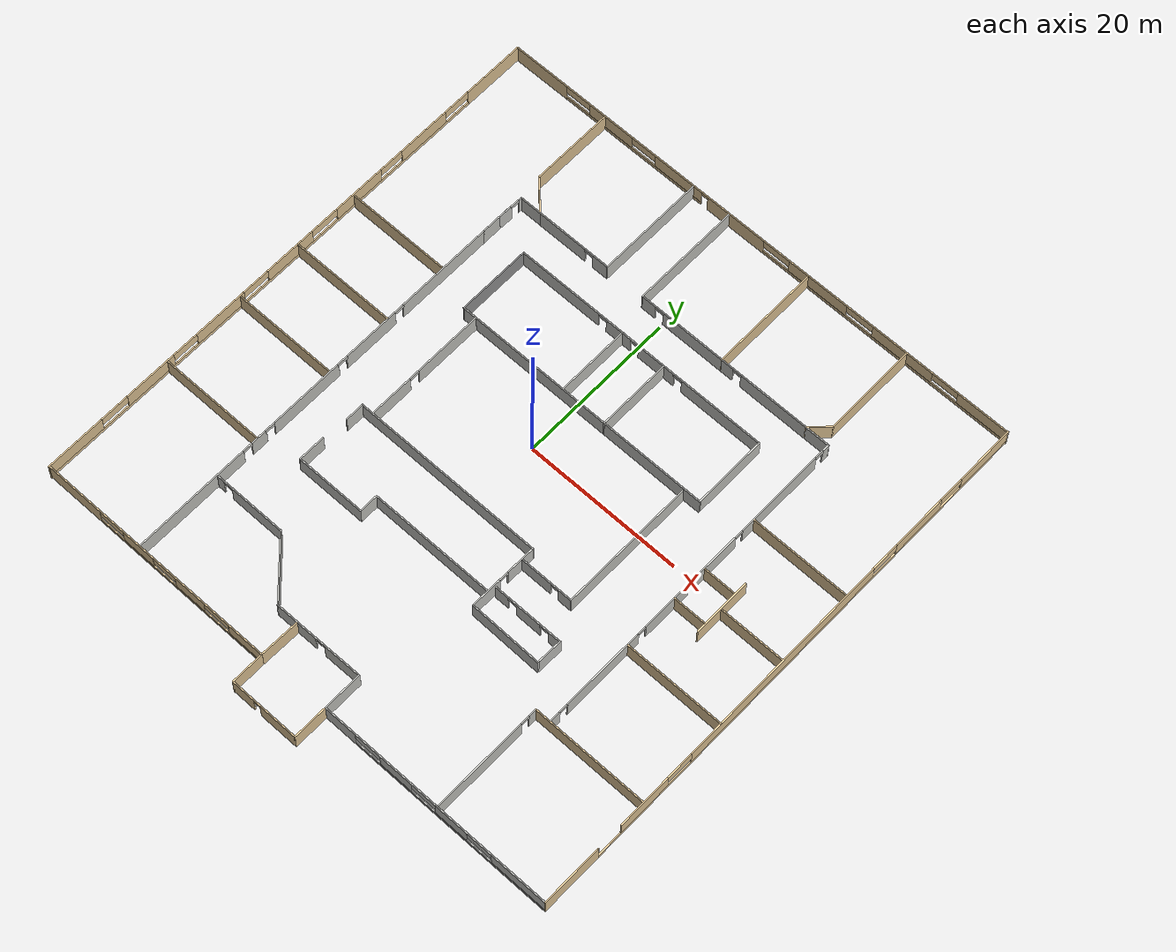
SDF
<?xml version='1.0'?>
<sdf version='1.6'>
  <model name='Building'>
    <pose frame=''>0.649204 -3.2026 0 0 -0 0</pose>
    <link name='Wall_10'>
      <pose frame=''>-19.5795 -33.75 0 0 -0 0</pose>
      <visual name='Wall_10_Visual_0'>
        <pose frame=''>-11.9192 0 1.25 0 -0 0</pose>
        <geometry>
          <box>
            <size>7.66158 0.15 2.5</size>
          </box>
        </geometry>
        <material>
          <script>
            <uri>file://media/materials/scripts/gazebo.material</uri>
            <name>Gazebo/Grey</name>
          </script>
          <ambient>0.921569 0.807843 0.615686 1</ambient>
        </material>
        <meta>
          <layer>0</layer>
        </meta>
      </visual>
      <collision name='Wall_10_Collision_0'>
        <geometry>
          <box>
            <size>7.66158 0.15 2.5</size>
          </box>
        </geometry>
        <pose frame=''>-11.9192 0 1.25 0 -0 0</pose>
      </collision>
      <visual name='Wall_10_Visual_1'>
        <pose frame=''>3.83079 0 0.25 0 -0 0</pose>
        <geometry>
          <box>
            <size>23.8384 0.15 0.5</size>
          </box>
        </geometry>
        <material>
          <script>
            <uri>file://media/materials/scripts/gazebo.material</uri>
            <name>Gazebo/Grey</name>
          </script>
          <ambient>0.921569 0.807843 0.615686 1</ambient>
        </material>
        <meta>
          <layer>0</layer>
        </meta>
      </visual>
      <collision name='Wall_10_Collision_1'>
        <geometry>
          <box>
            <size>23.8384 0.15 0.5</size>
          </box>
        </geometry>
        <pose frame=''>3.83079 0 0.25 0 -0 0</pose>
      </collision>
      <visual name='Wall_10_Visual_2'>
        <pose frame=''>-2.41376 0 1.5 0 -0 0</pose>
        <geometry>
          <box>
            <size>4.46303 0.15 2</size>
          </box>
        </geometry>
        <material>
          <script>
            <uri>file://media/materials/scripts/gazebo.material</uri>
            <name>Gazebo/Grey</name>
          </script>
          <ambient>0.921569 0.807843 0.615686 1</ambient>
        </material>
        <meta>
          <layer>0</layer>
        </meta>
      </visual>
      <collision name='Wall_10_Collision_2'>
        <geometry>
          <box>
            <size>4.46303 0.15 2</size>
          </box>
        </geometry>
        <pose frame=''>-2.41376 0 1.5 0 -0 0</pose>
      </collision>
      <visual name='Wall_10_Visual_3'>
        <pose frame=''>5.19728 0 1.5 0 -0 0</pose>
        <geometry>
          <box>
            <size>4.24144 0.15 2</size>
          </box>
        </geometry>
        <material>
          <script>
            <uri>file://media/materials/scripts/gazebo.material</uri>
            <name>Gazebo/Grey</name>
          </script>
          <ambient>0.921569 0.807843 0.615686 1</ambient>
        </material>
        <meta>
          <layer>0</layer>
        </meta>
      </visual>
      <collision name='Wall_10_Collision_3'>
        <geometry>
          <box>
            <size>4.24144 0.15 2</size>
          </box>
        </geometry>
        <pose frame=''>5.19728 0 1.5 0 -0 0</pose>
      </collision>
      <visual name='Wall_10_Visual_4'>
        <pose frame=''>13.3049 0 1.5 0 -0 0</pose>
        <geometry>
          <box>
            <size>4.89016 0.15 2</size>
          </box>
        </geometry>
        <material>
          <script>
            <uri>file://media/materials/scripts/gazebo.material</uri>
            <name>Gazebo/Grey</name>
          </script>
          <ambient>0.921569 0.807843 0.615686 1</ambient>
        </material>
        <meta>
          <layer>0</layer>
        </meta>
      </visual>
      <collision name='Wall_10_Collision_4'>
        <geometry>
          <box>
            <size>4.89016 0.15 2</size>
          </box>
        </geometry>
        <pose frame=''>13.3049 0 1.5 0 -0 0</pose>
      </collision>
      <visual name='Wall_10_Visual_5'>
        <pose frame=''>-6.36685 0 1.9 0 -0 0</pose>
        <geometry>
          <box>
            <size>3.44314 0.15 1.2</size>
          </box>
        </geometry>
        <material>
          <script>
            <uri>file://media/materials/scripts/gazebo.material</uri>
            <name>Gazebo/Grey</name>
          </script>
          <ambient>0.921569 0.807843 0.615686 1</ambient>
        </material>
        <meta>
          <layer>0</layer>
        </meta>
      </visual>
      <collision name='Wall_10_Collision_5'>
        <geometry>
          <box>
            <size>3.44314 0.15 1.2</size>
          </box>
        </geometry>
        <pose frame=''>-6.36685 0 1.9 0 -0 0</pose>
      </collision>
      <visual name='Wall_10_Visual_6'>
        <pose frame=''>1.44716 0 1.9 0 -0 0</pose>
        <geometry>
          <box>
            <size>3.25881 0.15 1.2</size>
          </box>
        </geometry>
        <material>
          <script>
            <uri>file://media/materials/scripts/gazebo.material</uri>
            <name>Gazebo/Grey</name>
          </script>
          <ambient>0.921569 0.807843 0.615686 1</ambient>
        </material>
        <meta>
          <layer>0</layer>
        </meta>
      </visual>
      <collision name='Wall_10_Collision_6'>
        <geometry>
          <box>
            <size>3.25881 0.15 1.2</size>
          </box>
        </geometry>
        <pose frame=''>1.44716 0 1.9 0 -0 0</pose>
      </collision>
      <visual name='Wall_10_Visual_7'>
        <pose frame=''>9.08892 0 1.9 0 -0 0</pose>
        <geometry>
          <box>
            <size>3.54184 0.15 1.2</size>
          </box>
        </geometry>
        <material>
          <script>
            <uri>file://media/materials/scripts/gazebo.material</uri>
            <name>Gazebo/Grey</name>
          </script>
          <ambient>0.921569 0.807843 0.615686 1</ambient>
        </material>
        <meta>
          <layer>0</layer>
        </meta>
      </visual>
      <collision name='Wall_10_Collision_7'>
        <geometry>
          <box>
            <size>3.54184 0.15 1.2</size>
          </box>
        </geometry>
        <pose frame=''>9.08892 0 1.9 0 -0 0</pose>
      </collision>
    </link>
    <link name='Wall_100'>
      <pose frame=''>12.7391 -11.9796 0 0 -0 3.14159</pose>
      <visual name='Wall_100_Visual_0'>
        <pose frame=''>-3.75183 0 1.25 0 -0 0</pose>
        <geometry>
          <box>
            <size>1.54633 0.15 2.5</size>
          </box>
        </geometry>
        <material>
          <script>
            <uri>file://media/materials/scripts/gazebo.material</uri>
            <name>Gazebo/CeilingTiled</name>
          </script>
          <ambient>1 1 1 1</ambient>
        </material>
        <meta>
          <layer>0</layer>
        </meta>
      </visual>
      <collision name='Wall_100_Collision_0'>
        <geometry>
          <box>
            <size>1.54633 0.15 2.5</size>
          </box>
        </geometry>
        <pose frame=''>-3.75183 0 1.25 0 -0 0</pose>
      </collision>
      <visual name='Wall_100_Visual_1'>
        <pose frame=''>-0.201089 0 1.25 0 -0 0</pose>
        <geometry>
          <box>
            <size>3.35516 0.15 2.5</size>
          </box>
        </geometry>
        <material>
          <script>
            <uri>file://media/materials/scripts/gazebo.material</uri>
            <name>Gazebo/CeilingTiled</name>
          </script>
          <ambient>1 1 1 1</ambient>
        </material>
        <meta>
          <layer>0</layer>
        </meta>
      </visual>
      <collision name='Wall_100_Collision_1'>
        <geometry>
          <box>
            <size>3.35516 0.15 2.5</size>
          </box>
        </geometry>
        <pose frame=''>-0.201089 0 1.25 0 -0 0</pose>
      </collision>
      <visual name='Wall_100_Visual_2'>
        <pose frame=''>3.55075 0 1.25 0 -0 0</pose>
        <geometry>
          <box>
            <size>1.94851 0.15 2.5</size>
          </box>
        </geometry>
        <material>
          <script>
            <uri>file://media/materials/scripts/gazebo.material</uri>
            <name>Gazebo/CeilingTiled</name>
          </script>
          <ambient>1 1 1 1</ambient>
        </material>
        <meta>
          <layer>0</layer>
        </meta>
      </visual>
      <collision name='Wall_100_Collision_2'>
        <geometry>
          <box>
            <size>1.94851 0.15 2.5</size>
          </box>
        </geometry>
        <pose frame=''>3.55075 0 1.25 0 -0 0</pose>
      </collision>
      <visual name='Wall_100_Visual_3'>
        <pose frame=''>-2.42867 0 2.25 0 -0 0</pose>
        <geometry>
          <box>
            <size>1.3 0.15 0.5</size>
          </box>
        </geometry>
        <material>
          <script>
            <uri>file://media/materials/scripts/gazebo.material</uri>
            <name>Gazebo/CeilingTiled</name>
          </script>
          <ambient>1 1 1 1</ambient>
        </material>
        <meta>
          <layer>0</layer>
        </meta>
      </visual>
      <collision name='Wall_100_Collision_3'>
        <geometry>
          <box>
            <size>1.3 0.15 0.5</size>
          </box>
        </geometry>
        <pose frame=''>-2.42867 0 2.25 0 -0 0</pose>
      </collision>
      <visual name='Wall_100_Visual_4'>
        <pose frame=''>2.02649 0 2.25 0 -0 0</pose>
        <geometry>
          <box>
            <size>1.3 0.15 0.5</size>
          </box>
        </geometry>
        <material>
          <script>
            <uri>file://media/materials/scripts/gazebo.material</uri>
            <name>Gazebo/CeilingTiled</name>
          </script>
          <ambient>1 1 1 1</ambient>
        </material>
        <meta>
          <layer>0</layer>
        </meta>
      </visual>
      <collision name='Wall_100_Collision_4'>
        <geometry>
          <box>
            <size>1.3 0.15 0.5</size>
          </box>
        </geometry>
        <pose frame=''>2.02649 0 2.25 0 -0 0</pose>
      </collision>
    </link>
    <link name='Wall_103'>
      <collision name='Wall_103_Collision'>
        <geometry>
          <box>
            <size>4.25 0.15 2.5</size>
          </box>
        </geometry>
        <pose frame=''>0 0 1.25 0 -0 0</pose>
      </collision>
      <visual name='Wall_103_Visual'>
        <pose frame=''>0 0 1.25 0 -0 0</pose>
        <geometry>
          <box>
            <size>4.25 0.15 2.5</size>
          </box>
        </geometry>
        <material>
          <script>
            <uri>file://media/materials/scripts/gazebo.material</uri>
            <name>Gazebo/Grey</name>
          </script>
          <ambient>0.921569 0.807843 0.615686 1</ambient>
        </material>
        <meta>
          <layer>0</layer>
        </meta>
      </visual>
      <pose frame=''>24.6252 4.22124 0 0 -0 0</pose>
    </link>
    <link name='Wall_105'>
      <collision name='Wall_105_Collision'>
        <geometry>
          <box>
            <size>4.25 0.15 2.5</size>
          </box>
        </geometry>
        <pose frame=''>0 0 1.25 0 -0 0</pose>
      </collision>
      <visual name='Wall_105_Visual'>
        <pose frame=''>0 0 1.25 0 -0 0</pose>
        <geometry>
          <box>
            <size>4.25 0.15 2.5</size>
          </box>
        </geometry>
        <material>
          <script>
            <uri>file://media/materials/scripts/gazebo.material</uri>
            <name>Gazebo/Grey</name>
          </script>
          <ambient>0.921569 0.807843 0.615686 1</ambient>
        </material>
        <meta>
          <layer>0</layer>
        </meta>
      </visual>
      <pose frame=''>24.6252 -0.368503 0 0 -0 0</pose>
    </link>
    <link name='Wall_107'>
      <collision name='Wall_107_Collision'>
        <geometry>
          <box>
            <size>7.5 0.15 2.5</size>
          </box>
        </geometry>
        <pose frame=''>0 0 1.25 0 -0 0</pose>
      </collision>
      <visual name='Wall_107_Visual'>
        <pose frame=''>0 0 1.25 0 -0 0</pose>
        <geometry>
          <box>
            <size>7.5 0.15 2.5</size>
          </box>
        </geometry>
        <material>
          <script>
            <uri>file://media/materials/scripts/gazebo.material</uri>
            <name>Gazebo/Grey</name>
          </script>
          <ambient>0.921569 0.807843 0.615686 1</ambient>
        </material>
        <meta>
          <layer>0</layer>
        </meta>
      </visual>
      <pose frame=''>26.8012 2.14732 0 0 0 -1.5708</pose>
    </link>
    <link name='Wall_109'>
      <collision name='Wall_109_Collision'>
        <geometry>
          <box>
            <size>8.5 0.15 2.5</size>
          </box>
        </geometry>
        <pose frame=''>0 0 1.25 0 -0 0</pose>
      </collision>
      <visual name='Wall_109_Visual'>
        <pose frame=''>0 0 1.25 0 -0 0</pose>
        <geometry>
          <box>
            <size>8.5 0.15 2.5</size>
          </box>
        </geometry>
        <material>
          <script>
            <uri>file://media/materials/scripts/gazebo.material</uri>
            <name>Gazebo/Grey</name>
          </script>
          <ambient>0.921569 0.807843 0.615686 1</ambient>
        </material>
        <meta>
          <layer>0</layer>
        </meta>
      </visual>
      <pose frame=''>31.0591 1.97974 0 0 -0 0</pose>
    </link>
    <link name='Wall_11'>
      <collision name='Wall_11_Collision'>
        <geometry>
          <box>
            <size>4.25 0.15 2.5</size>
          </box>
        </geometry>
        <pose frame=''>0 0 1.25 0 -0 0</pose>
      </collision>
      <visual name='Wall_11_Visual'>
        <pose frame=''>0 0 1.25 0 -0 0</pose>
        <geometry>
          <box>
            <size>4.25 0.15 2.5</size>
          </box>
        </geometry>
        <material>
          <script>
            <uri>file://media/materials/scripts/gazebo.material</uri>
            <name>Gazebo/Grey</name>
          </script>
          <ambient>0.921569 0.807843 0.615686 1</ambient>
        </material>
        <meta>
          <layer>0</layer>
        </meta>
      </visual>
      <pose frame=''>-3.9045 -35.8 0 0 0 -1.5708</pose>
    </link>
    <link name='Wall_12'>
      <pose frame=''>0.520502 -37.85 0 0 -0 0</pose>
      <visual name='Wall_12_Visual_0'>
        <pose frame=''>-2.96768 0 1.25 0 -0 0</pose>
        <geometry>
          <box>
            <size>3.06464 0.15 2.5</size>
          </box>
        </geometry>
        <material>
          <script>
            <uri>file://media/materials/scripts/gazebo.material</uri>
            <name>Gazebo/Grey</name>
          </script>
          <ambient>0.921569 0.807843 0.615686 1</ambient>
        </material>
        <meta>
          <layer>0</layer>
        </meta>
      </visual>
      <collision name='Wall_12_Collision_0'>
        <geometry>
          <box>
            <size>3.06464 0.15 2.5</size>
          </box>
        </geometry>
        <pose frame=''>-2.96768 0 1.25 0 -0 0</pose>
      </collision>
      <visual name='Wall_12_Visual_1'>
        <pose frame=''>1.98232 0 1.25 0 -0 0</pose>
        <geometry>
          <box>
            <size>5.03536 0.15 2.5</size>
          </box>
        </geometry>
        <material>
          <script>
            <uri>file://media/materials/scripts/gazebo.material</uri>
            <name>Gazebo/Grey</name>
          </script>
          <ambient>0.921569 0.807843 0.615686 1</ambient>
        </material>
        <meta>
          <layer>0</layer>
        </meta>
      </visual>
      <collision name='Wall_12_Collision_1'>
        <geometry>
          <box>
            <size>5.03536 0.15 2.5</size>
          </box>
        </geometry>
        <pose frame=''>1.98232 0 1.25 0 -0 0</pose>
      </collision>
      <visual name='Wall_12_Visual_2'>
        <pose frame=''>-0.985361 0 2.25 0 -0 0</pose>
        <geometry>
          <box>
            <size>0.9 0.15 0.5</size>
          </box>
        </geometry>
        <material>
          <script>
            <uri>file://media/materials/scripts/gazebo.material</uri>
            <name>Gazebo/Grey</name>
          </script>
          <ambient>0.921569 0.807843 0.615686 1</ambient>
        </material>
        <meta>
          <layer>0</layer>
        </meta>
      </visual>
      <collision name='Wall_12_Collision_2'>
        <geometry>
          <box>
            <size>0.9 0.15 0.5</size>
          </box>
        </geometry>
        <pose frame=''>-0.985361 0 2.25 0 -0 0</pose>
      </collision>
    </link>
    <link name='Wall_13'>
      <collision name='Wall_13_Collision'>
        <geometry>
          <box>
            <size>4.5 0.15 2.5</size>
          </box>
        </geometry>
        <pose frame=''>0 0 1.25 0 -0 0</pose>
      </collision>
      <visual name='Wall_13_Visual'>
        <pose frame=''>0 0 1.25 0 -0 0</pose>
        <geometry>
          <box>
            <size>4.5 0.15 2.5</size>
          </box>
        </geometry>
        <material>
          <script>
            <uri>file://media/materials/scripts/gazebo.material</uri>
            <name>Gazebo/Grey</name>
          </script>
          <ambient>0.921569 0.807843 0.615686 1</ambient>
        </material>
        <meta>
          <layer>0</layer>
        </meta>
      </visual>
      <pose frame=''>4.9455 -35.675 0 0 -0 1.5708</pose>
    </link>
    <link name='Wall_14'>
      <pose frame=''>20.1205 -33.5 0 0 -0 0</pose>
      <visual name='Wall_14_Visual_0'>
        <pose frame=''>-13.0855 0 1.25 0 -0 0</pose>
        <geometry>
          <box>
            <size>4.3291 0.15 2.5</size>
          </box>
        </geometry>
        <material>
          <script>
            <uri>file://media/materials/scripts/gazebo.material</uri>
            <name>Gazebo/CeilingTiled</name>
          </script>
          <ambient>0.921569 0.807843 0.615686 1</ambient>
        </material>
        <meta>
          <layer>0</layer>
        </meta>
      </visual>
      <collision name='Wall_14_Collision_0'>
        <geometry>
          <box>
            <size>4.3291 0.15 2.5</size>
          </box>
        </geometry>
        <pose frame=''>-13.0855 0 1.25 0 -0 0</pose>
      </collision>
      <visual name='Wall_14_Visual_1'>
        <pose frame=''>2.16455 0 0.25 0 -0 0</pose>
        <geometry>
          <box>
            <size>26.1709 0.15 0.5</size>
          </box>
        </geometry>
        <material>
          <script>
            <uri>file://media/materials/scripts/gazebo.material</uri>
            <name>Gazebo/CeilingTiled</name>
          </script>
          <ambient>0.921569 0.807843 0.615686 1</ambient>
        </material>
        <meta>
          <layer>0</layer>
        </meta>
      </visual>
      <collision name='Wall_14_Collision_1'>
        <geometry>
          <box>
            <size>26.1709 0.15 0.5</size>
          </box>
        </geometry>
        <pose frame=''>2.16455 0 0.25 0 -0 0</pose>
      </collision>
      <visual name='Wall_14_Visual_2'>
        <pose frame=''>-5.28013 0 1.5 0 -0 0</pose>
        <geometry>
          <box>
            <size>4.37212 0.15 2</size>
          </box>
        </geometry>
        <material>
          <script>
            <uri>file://media/materials/scripts/gazebo.material</uri>
            <name>Gazebo/CeilingTiled</name>
          </script>
          <ambient>0.921569 0.807843 0.615686 1</ambient>
        </material>
        <meta>
          <layer>0</layer>
        </meta>
      </visual>
      <collision name='Wall_14_Collision_2'>
        <geometry>
          <box>
            <size>4.37212 0.15 2</size>
          </box>
        </geometry>
        <pose frame=''>-5.28013 0 1.5 0 -0 0</pose>
      </collision>
      <visual name='Wall_14_Visual_3'>
        <pose frame=''>2.38651 0 1.5 0 -0 0</pose>
        <geometry>
          <box>
            <size>4.32635 0.15 2</size>
          </box>
        </geometry>
        <material>
          <script>
            <uri>file://media/materials/scripts/gazebo.material</uri>
            <name>Gazebo/CeilingTiled</name>
          </script>
          <ambient>0.921569 0.807843 0.615686 1</ambient>
        </material>
        <meta>
          <layer>0</layer>
        </meta>
      </visual>
      <collision name='Wall_14_Collision_3'>
        <geometry>
          <box>
            <size>4.32635 0.15 2</size>
          </box>
        </geometry>
        <pose frame=''>2.38651 0 1.5 0 -0 0</pose>
      </collision>
      <visual name='Wall_14_Visual_4'>
        <pose frame=''>11.5814 0 1.5 0 -0 0</pose>
        <geometry>
          <box>
            <size>7.33714 0.15 2</size>
          </box>
        </geometry>
        <material>
          <script>
            <uri>file://media/materials/scripts/gazebo.material</uri>
            <name>Gazebo/CeilingTiled</name>
          </script>
          <ambient>0.921569 0.807843 0.615686 1</ambient>
        </material>
        <meta>
          <layer>0</layer>
        </meta>
      </visual>
      <collision name='Wall_14_Collision_4'>
        <geometry>
          <box>
            <size>7.33714 0.15 2</size>
          </box>
        </geometry>
        <pose frame=''>11.5814 0 1.5 0 -0 0</pose>
      </collision>
      <visual name='Wall_14_Visual_5'>
        <pose frame=''>-9.19355 0 1.9 0 -0 0</pose>
        <geometry>
          <box>
            <size>3.45472 0.15 1.2</size>
          </box>
        </geometry>
        <material>
          <script>
            <uri>file://media/materials/scripts/gazebo.material</uri>
            <name>Gazebo/CeilingTiled</name>
          </script>
          <ambient>0.921569 0.807843 0.615686 1</ambient>
        </material>
        <meta>
          <layer>0</layer>
        </meta>
      </visual>
      <collision name='Wall_14_Collision_5'>
        <geometry>
          <box>
            <size>3.45472 0.15 1.2</size>
          </box>
        </geometry>
        <pose frame=''>-9.19355 0 1.9 0 -0 0</pose>
      </collision>
      <visual name='Wall_14_Visual_6'>
        <pose frame=''>-1.43537 0 1.9 0 -0 0</pose>
        <geometry>
          <box>
            <size>3.3174 0.15 1.2</size>
          </box>
        </geometry>
        <material>
          <script>
            <uri>file://media/materials/scripts/gazebo.material</uri>
            <name>Gazebo/CeilingTiled</name>
          </script>
          <ambient>0.921569 0.807843 0.615686 1</ambient>
        </material>
        <meta>
          <layer>0</layer>
        </meta>
      </visual>
      <collision name='Wall_14_Collision_6'>
        <geometry>
          <box>
            <size>3.3174 0.15 1.2</size>
          </box>
        </geometry>
        <pose frame=''>-1.43537 0 1.9 0 -0 0</pose>
      </collision>
      <visual name='Wall_14_Visual_7'>
        <pose frame=''>6.23127 0 1.9 0 -0 0</pose>
        <geometry>
          <box>
            <size>3.36317 0.15 1.2</size>
          </box>
        </geometry>
        <material>
          <script>
            <uri>file://media/materials/scripts/gazebo.material</uri>
            <name>Gazebo/CeilingTiled</name>
          </script>
          <ambient>0.921569 0.807843 0.615686 1</ambient>
        </material>
        <meta>
          <layer>0</layer>
        </meta>
      </visual>
      <collision name='Wall_14_Collision_7'>
        <geometry>
          <box>
            <size>3.36317 0.15 1.2</size>
          </box>
        </geometry>
        <pose frame=''>6.23127 0 1.9 0 -0 0</pose>
      </collision>
    </link>
    <link name='Wall_15'>
      <pose frame=''>35.2955 2.175 0 0 -0 1.5708</pose>
      <visual name='Wall_15_Visual_0'>
        <pose frame=''>-31.881 0 1.25 0 -0 0</pose>
        <geometry>
          <box>
            <size>7.73799 0.15 2.5</size>
          </box>
        </geometry>
        <material>
          <script>
            <uri>file://media/materials/scripts/gazebo.material</uri>
            <name>Gazebo/Grey</name>
          </script>
          <ambient>0.921569 0.807843 0.615686 1</ambient>
        </material>
        <meta>
          <layer>0</layer>
        </meta>
      </visual>
      <collision name='Wall_15_Collision_0'>
        <geometry>
          <box>
            <size>7.73799 0.15 2.5</size>
          </box>
        </geometry>
        <pose frame=''>-31.881 0 1.25 0 -0 0</pose>
      </collision>
      <visual name='Wall_15_Visual_1'>
        <pose frame=''>3.869 0 0.25 0 -0 0</pose>
        <geometry>
          <box>
            <size>63.762 0.15 0.5</size>
          </box>
        </geometry>
        <material>
          <script>
            <uri>file://media/materials/scripts/gazebo.material</uri>
            <name>Gazebo/Grey</name>
          </script>
          <ambient>0.921569 0.807843 0.615686 1</ambient>
        </material>
        <meta>
          <layer>0</layer>
        </meta>
      </visual>
      <collision name='Wall_15_Collision_1'>
        <geometry>
          <box>
            <size>63.762 0.15 0.5</size>
          </box>
        </geometry>
        <pose frame=''>3.869 0 0.25 0 -0 0</pose>
      </collision>
      <visual name='Wall_15_Visual_2'>
        <pose frame=''>-21.1676 0 1.5 0 -0 0</pose>
        <geometry>
          <box>
            <size>6.97218 0.15 2</size>
          </box>
        </geometry>
        <material>
          <script>
            <uri>file://media/materials/scripts/gazebo.material</uri>
            <name>Gazebo/Grey</name>
          </script>
          <ambient>0.921569 0.807843 0.615686 1</ambient>
        </material>
        <meta>
          <layer>0</layer>
        </meta>
      </visual>
      <collision name='Wall_15_Collision_2'>
        <geometry>
          <box>
            <size>6.97218 0.15 2</size>
          </box>
        </geometry>
        <pose frame=''>-21.1676 0 1.5 0 -0 0</pose>
      </collision>
      <visual name='Wall_15_Visual_3'>
        <pose frame=''>-0.106032 0 1.5 0 -0 0</pose>
        <geometry>
          <box>
            <size>28.1209 0.15 2</size>
          </box>
        </geometry>
        <material>
          <script>
            <uri>file://media/materials/scripts/gazebo.material</uri>
            <name>Gazebo/Grey</name>
          </script>
          <ambient>0.921569 0.807843 0.615686 1</ambient>
        </material>
        <meta>
          <layer>0</layer>
        </meta>
      </visual>
      <collision name='Wall_15_Collision_3'>
        <geometry>
          <box>
            <size>28.1209 0.15 2</size>
          </box>
        </geometry>
        <pose frame=''>-0.106032 0 1.5 0 -0 0</pose>
      </collision>
      <visual name='Wall_15_Visual_4'>
        <pose frame=''>21.1713 0 1.5 0 -0 0</pose>
        <geometry>
          <box>
            <size>7.19064 0.15 2</size>
          </box>
        </geometry>
        <material>
          <script>
            <uri>file://media/materials/scripts/gazebo.material</uri>
            <name>Gazebo/Grey</name>
          </script>
          <ambient>0.921569 0.807843 0.615686 1</ambient>
        </material>
        <meta>
          <layer>0</layer>
        </meta>
      </visual>
      <collision name='Wall_15_Collision_4'>
        <geometry>
          <box>
            <size>7.19064 0.15 2</size>
          </box>
        </geometry>
        <pose frame=''>21.1713 0 1.5 0 -0 0</pose>
      </collision>
      <visual name='Wall_15_Visual_5'>
        <pose frame=''>31.8827 0 1.5 0 -0 0</pose>
        <geometry>
          <box>
            <size>7.73457 0.15 2</size>
          </box>
        </geometry>
        <material>
          <script>
            <uri>file://media/materials/scripts/gazebo.material</uri>
            <name>Gazebo/Grey</name>
          </script>
          <ambient>0.921569 0.807843 0.615686 1</ambient>
        </material>
        <meta>
          <layer>0</layer>
        </meta>
      </visual>
      <collision name='Wall_15_Collision_5'>
        <geometry>
          <box>
            <size>7.73457 0.15 2</size>
          </box>
        </geometry>
        <pose frame=''>31.8827 0 1.5 0 -0 0</pose>
      </collision>
      <visual name='Wall_15_Visual_6'>
        <pose frame=''>-27.9687 0 1.9 0 -0 0</pose>
        <geometry>
          <box>
            <size>0.086667 0.15 1.2</size>
          </box>
        </geometry>
        <material>
          <script>
            <uri>file://media/materials/scripts/gazebo.material</uri>
            <name>Gazebo/Grey</name>
          </script>
          <ambient>0.921569 0.807843 0.615686 1</ambient>
        </material>
        <meta>
          <layer>0</layer>
        </meta>
      </visual>
      <collision name='Wall_15_Collision_6'>
        <geometry>
          <box>
            <size>0.086667 0.15 1.2</size>
          </box>
        </geometry>
        <pose frame=''>-27.9687 0 1.9 0 -0 0</pose>
      </collision>
      <visual name='Wall_15_Visual_7'>
        <pose frame=''>-15.924 0 1.9 0 -0 0</pose>
        <geometry>
          <box>
            <size>3.51504 0.15 1.2</size>
          </box>
        </geometry>
        <material>
          <script>
            <uri>file://media/materials/scripts/gazebo.material</uri>
            <name>Gazebo/Grey</name>
          </script>
          <ambient>0.921569 0.807843 0.615686 1</ambient>
        </material>
        <meta>
          <layer>0</layer>
        </meta>
      </visual>
      <collision name='Wall_15_Collision_7'>
        <geometry>
          <box>
            <size>3.51504 0.15 1.2</size>
          </box>
        </geometry>
        <pose frame=''>-15.924 0 1.9 0 -0 0</pose>
      </collision>
      <visual name='Wall_15_Visual_8'>
        <pose frame=''>15.7652 0 1.9 0 -0 0</pose>
        <geometry>
          <box>
            <size>3.62151 0.15 1.2</size>
          </box>
        </geometry>
        <material>
          <script>
            <uri>file://media/materials/scripts/gazebo.material</uri>
            <name>Gazebo/Grey</name>
          </script>
          <ambient>0.921569 0.807843 0.615686 1</ambient>
        </material>
        <meta>
          <layer>0</layer>
        </meta>
      </visual>
      <collision name='Wall_15_Collision_8'>
        <geometry>
          <box>
            <size>3.62151 0.15 1.2</size>
          </box>
        </geometry>
        <pose frame=''>15.7652 0 1.9 0 -0 0</pose>
      </collision>
      <visual name='Wall_15_Visual_9'>
        <pose frame=''>26.391 0 1.9 0 -0 0</pose>
        <geometry>
          <box>
            <size>3.24886 0.15 1.2</size>
          </box>
        </geometry>
        <material>
          <script>
            <uri>file://media/materials/scripts/gazebo.material</uri>
            <name>Gazebo/Grey</name>
          </script>
          <ambient>0.921569 0.807843 0.615686 1</ambient>
        </material>
        <meta>
          <layer>0</layer>
        </meta>
      </visual>
      <collision name='Wall_15_Collision_9'>
        <geometry>
          <box>
            <size>3.24886 0.15 1.2</size>
          </box>
        </geometry>
        <pose frame=''>26.391 0 1.9 0 -0 0</pose>
      </collision>
    </link>
    <link name='Wall_181'>
      <pose frame=''>8.05273 -10.6417 0 0 -0 1.55946</pose>
      <visual name='Wall_181_Visual_0'>
        <pose frame=''>-2.4226 0 1.25 0 -0 0</pose>
        <geometry>
          <box>
            <size>3.9635 0.15 2.5</size>
          </box>
        </geometry>
        <material>
          <script>
            <uri>file://media/materials/scripts/gazebo.material</uri>
            <name>Gazebo/CeilingTiled</name>
          </script>
          <ambient>1 1 1 1</ambient>
        </material>
        <meta>
          <layer>0</layer>
        </meta>
      </visual>
      <collision name='Wall_181_Collision_0'>
        <geometry>
          <box>
            <size>4.1635 0.15 2.5</size>
          </box>
        </geometry>
        <pose frame=''>-2.4226 0 1.25 0 -0 0</pose>
      </collision>
      <visual name='Wall_181_Visual_1'>
        <pose frame=''>2.53175 0 1.25 0 -0 0</pose>
        <geometry>
          <box>
            <size>3.74519 0.15 2.5</size>
          </box>
        </geometry>
        <material>
          <script>
            <uri>file://media/materials/scripts/gazebo.material</uri>
            <name>Gazebo/CeilingTiled</name>
          </script>
          <ambient>1 1 1 1</ambient>
        </material>
        <meta>
          <layer>0</layer>
        </meta>
      </visual>
      <collision name='Wall_181_Collision_1'>
        <geometry>
          <box>
            <size>3.94519 0.15 2.5</size>
          </box>
        </geometry>
        <pose frame=''>2.53175 0 1.25 0 -0 0</pose>
      </collision>
      <visual name='Wall_181_Visual_2'>
        <pose frame=''>0.109156 0 2.25 0 -0 0</pose>
        <geometry>
          <box>
            <size>1.3 0.15 0.5</size>
          </box>
        </geometry>
        <material>
          <script>
            <uri>file://media/materials/scripts/gazebo.material</uri>
            <name>Gazebo/CeilingTiled</name>
          </script>
          <ambient>1 1 1 1</ambient>
        </material>
        <meta>
          <layer>0</layer>
        </meta>
      </visual>
      <collision name='Wall_181_Collision_2'>
        <geometry>
          <box>
            <size>0.9 0.15 0.5</size>
          </box>
        </geometry>
        <pose frame=''>0.109156 0 2.25 0 -0 0</pose>
      </collision>
    </link>
    <link name='Wall_19'>
      <pose frame=''>0.058011 37.7805 0 0 -0 0</pose>
      <visual name='Wall_19_Visual_0'>
        <pose frame=''>-31.6032 0 1.25 0 -0 0</pose>
        <geometry>
          <box>
            <size>7.48557 0.15 2.5</size>
          </box>
        </geometry>
        <material>
          <script>
            <uri>file://media/materials/scripts/gazebo.material</uri>
            <name>Gazebo/Grey</name>
          </script>
          <ambient>0.921569 0.807843 0.615686 1</ambient>
        </material>
        <meta>
          <layer>0</layer>
        </meta>
      </visual>
      <collision name='Wall_19_Collision_0'>
        <geometry>
          <box>
            <size>7.48557 0.15 2.5</size>
          </box>
        </geometry>
        <pose frame=''>-31.6032 0 1.25 0 -0 0</pose>
      </collision>
      <visual name='Wall_19_Visual_1'>
        <pose frame=''>-2.88179 0 1.25 0 -0 0</pose>
        <geometry>
          <box>
            <size>8.13835 0.15 2.5</size>
          </box>
        </geometry>
        <material>
          <script>
            <uri>file://media/materials/scripts/gazebo.material</uri>
            <name>Gazebo/Grey</name>
          </script>
          <ambient>0.921569 0.807843 0.615686 1</ambient>
        </material>
        <meta>
          <layer>0</layer>
        </meta>
      </visual>
      <collision name='Wall_19_Collision_1'>
        <geometry>
          <box>
            <size>8.13835 0.15 2.5</size>
          </box>
        </geometry>
        <pose frame=''>-2.88179 0 1.25 0 -0 0</pose>
      </collision>
      <visual name='Wall_19_Visual_2'>
        <pose frame=''>-17.8557 0 0.25 0 -0 0</pose>
        <geometry>
          <box>
            <size>20.0095 0.15 0.5</size>
          </box>
        </geometry>
        <material>
          <script>
            <uri>file://media/materials/scripts/gazebo.material</uri>
            <name>Gazebo/Grey</name>
          </script>
          <ambient>0.921569 0.807843 0.615686 1</ambient>
        </material>
        <meta>
          <layer>0</layer>
        </meta>
      </visual>
      <collision name='Wall_19_Collision_2'>
        <geometry>
          <box>
            <size>20.0095 0.15 0.5</size>
          </box>
        </geometry>
        <pose frame=''>-17.8557 0 0.25 0 -0 0</pose>
      </collision>
      <visual name='Wall_19_Visual_3'>
        <pose frame=''>18.2667 0 0.25 0 -0 0</pose>
        <geometry>
          <box>
            <size>34.1586 0.15 0.5</size>
          </box>
        </geometry>
        <material>
          <script>
            <uri>file://media/materials/scripts/gazebo.material</uri>
            <name>Gazebo/Grey</name>
          </script>
          <ambient>0.921569 0.807843 0.615686 1</ambient>
        </material>
        <meta>
          <layer>0</layer>
        </meta>
      </visual>
      <collision name='Wall_19_Collision_3'>
        <geometry>
          <box>
            <size>34.1586 0.15 0.5</size>
          </box>
        </geometry>
        <pose frame=''>18.2667 0 0.25 0 -0 0</pose>
      </collision>
      <visual name='Wall_19_Visual_4'>
        <pose frame=''>-21.2381 0 1.5 0 -0 0</pose>
        <geometry>
          <box>
            <size>6.36726 0.15 2</size>
          </box>
        </geometry>
        <material>
          <script>
            <uri>file://media/materials/scripts/gazebo.material</uri>
            <name>Gazebo/Grey</name>
          </script>
          <ambient>0.921569 0.807843 0.615686 1</ambient>
        </material>
        <meta>
          <layer>0</layer>
        </meta>
      </visual>
      <collision name='Wall_19_Collision_4'>
        <geometry>
          <box>
            <size>6.36726 0.15 2</size>
          </box>
        </geometry>
        <pose frame=''>-21.2381 0 1.5 0 -0 0</pose>
      </collision>
      <visual name='Wall_19_Visual_5'>
        <pose frame=''>-11.2566 0 1.5 0 -0 0</pose>
        <geometry>
          <box>
            <size>6.81117 0.15 2</size>
          </box>
        </geometry>
        <material>
          <script>
            <uri>file://media/materials/scripts/gazebo.material</uri>
            <name>Gazebo/Grey</name>
          </script>
          <ambient>0.921569 0.807843 0.615686 1</ambient>
        </material>
        <meta>
          <layer>0</layer>
        </meta>
      </visual>
      <collision name='Wall_19_Collision_5'>
        <geometry>
          <box>
            <size>6.81117 0.15 2</size>
          </box>
        </geometry>
        <pose frame=''>-11.2566 0 1.5 0 -0 0</pose>
      </collision>
      <visual name='Wall_19_Visual_6'>
        <pose frame=''>-11.2566 0 1.5 0 -0 0</pose>
        <geometry>
          <box>
            <size>6.81117 0.15 2</size>
          </box>
        </geometry>
        <material>
          <script>
            <uri>file://media/materials/scripts/gazebo.material</uri>
            <name>Gazebo/Grey</name>
          </script>
          <ambient>0.921569 0.807843 0.615686 1</ambient>
        </material>
        <meta>
          <layer>0</layer>
        </meta>
      </visual>
      <collision name='Wall_19_Collision_6'>
        <geometry>
          <box>
            <size>6.81117 0.15 2</size>
          </box>
        </geometry>
        <pose frame=''>-11.2566 0 1.5 0 -0 0</pose>
      </collision>
      <visual name='Wall_19_Visual_7'>
        <pose frame=''>8.90248 0 1.5 0 -0 0</pose>
        <geometry>
          <box>
            <size>8.18717 0.15 2</size>
          </box>
        </geometry>
        <material>
          <script>
            <uri>file://media/materials/scripts/gazebo.material</uri>
            <name>Gazebo/Grey</name>
          </script>
          <ambient>0.921569 0.807843 0.615686 1</ambient>
        </material>
        <meta>
          <layer>0</layer>
        </meta>
      </visual>
      <collision name='Wall_19_Collision_7'>
        <geometry>
          <box>
            <size>8.18717 0.15 2</size>
          </box>
        </geometry>
        <pose frame=''>8.90248 0 1.5 0 -0 0</pose>
      </collision>
      <visual name='Wall_19_Visual_8'>
        <pose frame=''>20.8176 0 1.5 0 -0 0</pose>
        <geometry>
          <box>
            <size>8.2936 0.15 2</size>
          </box>
        </geometry>
        <material>
          <script>
            <uri>file://media/materials/scripts/gazebo.material</uri>
            <name>Gazebo/Grey</name>
          </script>
          <ambient>0.921569 0.807843 0.615686 1</ambient>
        </material>
        <meta>
          <layer>0</layer>
        </meta>
      </visual>
      <collision name='Wall_19_Collision_8'>
        <geometry>
          <box>
            <size>8.2936 0.15 2</size>
          </box>
        </geometry>
        <pose frame=''>20.8176 0 1.5 0 -0 0</pose>
      </collision>
      <visual name='Wall_19_Visual_9'>
        <pose frame=''>31.9127 0 1.5 0 -0 0</pose>
        <geometry>
          <box>
            <size>6.86653 0.15 2</size>
          </box>
        </geometry>
        <material>
          <script>
            <uri>file://media/materials/scripts/gazebo.material</uri>
            <name>Gazebo/Grey</name>
          </script>
          <ambient>0.921569 0.807843 0.615686 1</ambient>
        </material>
        <meta>
          <layer>0</layer>
        </meta>
      </visual>
      <collision name='Wall_19_Collision_9'>
        <geometry>
          <box>
            <size>6.86653 0.15 2</size>
          </box>
        </geometry>
        <pose frame=''>31.9127 0 1.5 0 -0 0</pose>
      </collision>
      <visual name='Wall_19_Visual_10'>
        <pose frame=''>-26.1411 0 1.9 0 -0 0</pose>
        <geometry>
          <box>
            <size>3.43866 0.15 1.2</size>
          </box>
        </geometry>
        <material>
          <script>
            <uri>file://media/materials/scripts/gazebo.material</uri>
            <name>Gazebo/Grey</name>
          </script>
          <ambient>0.921569 0.807843 0.615686 1</ambient>
        </material>
        <meta>
          <layer>0</layer>
        </meta>
      </visual>
      <collision name='Wall_19_Collision_10'>
        <geometry>
          <box>
            <size>3.43866 0.15 1.2</size>
          </box>
        </geometry>
        <pose frame=''>-26.1411 0 1.9 0 -0 0</pose>
      </collision>
      <visual name='Wall_19_Visual_11'>
        <pose frame=''>2.99814 0 1.9 0 -0 0</pose>
        <geometry>
          <box>
            <size>3.62151 0.15 1.2</size>
          </box>
        </geometry>
        <material>
          <script>
            <uri>file://media/materials/scripts/gazebo.material</uri>
            <name>Gazebo/Grey</name>
          </script>
          <ambient>0.921569 0.807843 0.615686 1</ambient>
        </material>
        <meta>
          <layer>0</layer>
        </meta>
      </visual>
      <collision name='Wall_19_Collision_11'>
        <geometry>
          <box>
            <size>3.62151 0.15 1.2</size>
          </box>
        </geometry>
        <pose frame=''>2.99814 0 1.9 0 -0 0</pose>
      </collision>
      <visual name='Wall_19_Visual_12'>
        <pose frame=''>-16.3583 0 1.9 0 -0 0</pose>
        <geometry>
          <box>
            <size>3.39237 0.15 1.2</size>
          </box>
        </geometry>
        <material>
          <script>
            <uri>file://media/materials/scripts/gazebo.material</uri>
            <name>Gazebo/Grey</name>
          </script>
          <ambient>0.921569 0.807843 0.615686 1</ambient>
        </material>
        <meta>
          <layer>0</layer>
        </meta>
      </visual>
      <collision name='Wall_19_Collision_12'>
        <geometry>
          <box>
            <size>3.39237 0.15 1.2</size>
          </box>
        </geometry>
        <pose frame=''>-16.3583 0 1.9 0 -0 0</pose>
      </collision>
      <visual name='Wall_19_Visual_13'>
        <pose frame=''>14.8334 0 1.9 0 -0 0</pose>
        <geometry>
          <box>
            <size>3.67475 0.15 1.2</size>
          </box>
        </geometry>
        <material>
          <script>
            <uri>file://media/materials/scripts/gazebo.material</uri>
            <name>Gazebo/Grey</name>
          </script>
          <ambient>0.921569 0.807843 0.615686 1</ambient>
        </material>
        <meta>
          <layer>0</layer>
        </meta>
      </visual>
      <collision name='Wall_19_Collision_13'>
        <geometry>
          <box>
            <size>3.67475 0.15 1.2</size>
          </box>
        </geometry>
        <pose frame=''>14.8334 0 1.9 0 -0 0</pose>
      </collision>
      <visual name='Wall_19_Visual_14'>
        <pose frame=''>26.7219 0 1.9 0 -0 0</pose>
        <geometry>
          <box>
            <size>3.51504 0.15 1.2</size>
          </box>
        </geometry>
        <material>
          <script>
            <uri>file://media/materials/scripts/gazebo.material</uri>
            <name>Gazebo/Grey</name>
          </script>
          <ambient>0.921569 0.807843 0.615686 1</ambient>
        </material>
        <meta>
          <layer>0</layer>
        </meta>
      </visual>
      <collision name='Wall_19_Collision_14'>
        <geometry>
          <box>
            <size>3.51504 0.15 1.2</size>
          </box>
        </geometry>
        <pose frame=''>26.7219 0 1.9 0 -0 0</pose>
      </collision>
      <visual name='Wall_19_Visual_15'>
        <pose frame=''>-7.40097 0 2.25 0 -0 0</pose>
        <geometry>
          <box>
            <size>0.9 0.15 0.5</size>
          </box>
        </geometry>
        <material>
          <script>
            <uri>file://media/materials/scripts/gazebo.material</uri>
            <name>Gazebo/Grey</name>
          </script>
          <ambient>0.921569 0.807843 0.615686 1</ambient>
        </material>
        <meta>
          <layer>0</layer>
        </meta>
      </visual>
      <collision name='Wall_19_Collision_15'>
        <geometry>
          <box>
            <size>0.9 0.15 0.5</size>
          </box>
        </geometry>
        <pose frame=''>-7.40097 0 2.25 0 -0 0</pose>
      </collision>
      <visual name='Wall_19_Visual_16'>
        <pose frame=''>-7.40097 0 2.25 0 -0 0</pose>
        <geometry>
          <box>
            <size>0.9 0.15 0.5</size>
          </box>
        </geometry>
        <material>
          <script>
            <uri>file://media/materials/scripts/gazebo.material</uri>
            <name>Gazebo/Grey</name>
          </script>
          <ambient>0.921569 0.807843 0.615686 1</ambient>
        </material>
        <meta>
          <layer>0</layer>
        </meta>
      </visual>
      <collision name='Wall_19_Collision_16'>
        <geometry>
          <box>
            <size>0.9 0.15 0.5</size>
          </box>
        </geometry>
        <pose frame=''>-7.40097 0 2.25 0 -0 0</pose>
      </collision>
    </link>
    <link name='Wall_2'>
      <pose frame=''>-35.329 1.98049 0 0 0 -1.5708</pose>
      <visual name='Wall_2_Visual_0'>
        <pose frame=''>-31.7867 0 1.25 0 -0 0</pose>
        <geometry>
          <box>
            <size>8.1767 0.15 2.5</size>
          </box>
        </geometry>
        <material>
          <script>
            <uri>file://media/materials/scripts/gazebo.material</uri>
            <name>Gazebo/Grey</name>
          </script>
          <ambient>0.921569 0.807843 0.615686 1</ambient>
        </material>
        <meta>
          <layer>0</layer>
        </meta>
      </visual>
      <collision name='Wall_2_Collision_0'>
        <geometry>
          <box>
            <size>8.1767 0.15 2.5</size>
          </box>
        </geometry>
        <pose frame=''>-31.7867 0 1.25 0 -0 0</pose>
      </collision>
      <visual name='Wall_2_Visual_1'>
        <pose frame=''>4.08835 0 0.25 0 -0 0</pose>
        <geometry>
          <box>
            <size>63.5733 0.15 0.5</size>
          </box>
        </geometry>
        <material>
          <script>
            <uri>file://media/materials/scripts/gazebo.material</uri>
            <name>Gazebo/Grey</name>
          </script>
          <ambient>0.921569 0.807843 0.615686 1</ambient>
        </material>
        <meta>
          <layer>0</layer>
        </meta>
      </visual>
      <collision name='Wall_2_Collision_1'>
        <geometry>
          <box>
            <size>63.5733 0.15 0.5</size>
          </box>
        </geometry>
        <pose frame=''>4.08835 0 0.25 0 -0 0</pose>
      </collision>
      <visual name='Wall_2_Visual_2'>
        <pose frame=''>-20.6272 0 1.5 0 -0 0</pose>
        <geometry>
          <box>
            <size>6.88516 0.15 2</size>
          </box>
        </geometry>
        <material>
          <script>
            <uri>file://media/materials/scripts/gazebo.material</uri>
            <name>Gazebo/Grey</name>
          </script>
          <ambient>0.921569 0.807843 0.615686 1</ambient>
        </material>
        <meta>
          <layer>0</layer>
        </meta>
      </visual>
      <collision name='Wall_2_Collision_2'>
        <geometry>
          <box>
            <size>6.88516 0.15 2</size>
          </box>
        </geometry>
        <pose frame=''>-20.6272 0 1.5 0 -0 0</pose>
      </collision>
      <visual name='Wall_2_Visual_3'>
        <pose frame=''>-10.487 0 1.5 0 -0 0</pose>
        <geometry>
          <box>
            <size>6.88516 0.15 2</size>
          </box>
        </geometry>
        <material>
          <script>
            <uri>file://media/materials/scripts/gazebo.material</uri>
            <name>Gazebo/Grey</name>
          </script>
          <ambient>0.921569 0.807843 0.615686 1</ambient>
        </material>
        <meta>
          <layer>0</layer>
        </meta>
      </visual>
      <collision name='Wall_2_Collision_3'>
        <geometry>
          <box>
            <size>6.88516 0.15 2</size>
          </box>
        </geometry>
        <pose frame=''>-10.487 0 1.5 0 -0 0</pose>
      </collision>
      <visual name='Wall_2_Visual_4'>
        <pose frame=''>0.140779 0 1.5 0 -0 0</pose>
        <geometry>
          <box>
            <size>6.7931 0.15 2</size>
          </box>
        </geometry>
        <material>
          <script>
            <uri>file://media/materials/scripts/gazebo.material</uri>
            <name>Gazebo/Grey</name>
          </script>
          <ambient>0.921569 0.807843 0.615686 1</ambient>
        </material>
        <meta>
          <layer>0</layer>
        </meta>
      </visual>
      <collision name='Wall_2_Collision_4'>
        <geometry>
          <box>
            <size>6.7931 0.15 2</size>
          </box>
        </geometry>
        <pose frame=''>0.140779 0 1.5 0 -0 0</pose>
      </collision>
      <visual name='Wall_2_Visual_5'>
        <pose frame=''>10.6748 0 1.5 0 -0 0</pose>
        <geometry>
          <box>
            <size>7.0604 0.15 2</size>
          </box>
        </geometry>
        <material>
          <script>
            <uri>file://media/materials/scripts/gazebo.material</uri>
            <name>Gazebo/Grey</name>
          </script>
          <ambient>0.921569 0.807843 0.615686 1</ambient>
        </material>
        <meta>
          <layer>0</layer>
        </meta>
      </visual>
      <collision name='Wall_2_Collision_5'>
        <geometry>
          <box>
            <size>7.0604 0.15 2</size>
          </box>
        </geometry>
        <pose frame=''>10.6748 0 1.5 0 -0 0</pose>
      </collision>
      <visual name='Wall_2_Visual_6'>
        <pose frame=''>21.0585 0 1.5 0 -0 0</pose>
        <geometry>
          <box>
            <size>6.84339 0.15 2</size>
          </box>
        </geometry>
        <material>
          <script>
            <uri>file://media/materials/scripts/gazebo.material</uri>
            <name>Gazebo/Grey</name>
          </script>
          <ambient>0.921569 0.807843 0.615686 1</ambient>
        </material>
        <meta>
          <layer>0</layer>
        </meta>
      </visual>
      <collision name='Wall_2_Collision_6'>
        <geometry>
          <box>
            <size>6.84339 0.15 2</size>
          </box>
        </geometry>
        <pose frame=''>21.0585 0 1.5 0 -0 0</pose>
      </collision>
      <visual name='Wall_2_Visual_7'>
        <pose frame=''>32.0339 0 1.5 0 -0 0</pose>
        <geometry>
          <box>
            <size>7.68221 0.15 2</size>
          </box>
        </geometry>
        <material>
          <script>
            <uri>file://media/materials/scripts/gazebo.material</uri>
            <name>Gazebo/Grey</name>
          </script>
          <ambient>0.921569 0.807843 0.615686 1</ambient>
        </material>
        <meta>
          <layer>0</layer>
        </meta>
      </visual>
      <collision name='Wall_2_Collision_7'>
        <geometry>
          <box>
            <size>7.68221 0.15 2</size>
          </box>
        </geometry>
        <pose frame=''>32.0339 0 1.5 0 -0 0</pose>
      </collision>
      <visual name='Wall_2_Visual_8'>
        <pose frame=''>-25.884 0 1.9 0 -0 0</pose>
        <geometry>
          <box>
            <size>3.62857 0.15 1.2</size>
          </box>
        </geometry>
        <material>
          <script>
            <uri>file://media/materials/scripts/gazebo.material</uri>
            <name>Gazebo/Grey</name>
          </script>
          <ambient>0.921569 0.807843 0.615686 1</ambient>
        </material>
        <meta>
          <layer>0</layer>
        </meta>
      </visual>
      <collision name='Wall_2_Collision_8'>
        <geometry>
          <box>
            <size>3.62857 0.15 1.2</size>
          </box>
        </geometry>
        <pose frame=''>-25.884 0 1.9 0 -0 0</pose>
      </collision>
      <visual name='Wall_2_Visual_9'>
        <pose frame=''>-15.5571 0 1.9 0 -0 0</pose>
        <geometry>
          <box>
            <size>3.25498 0.15 1.2</size>
          </box>
        </geometry>
        <material>
          <script>
            <uri>file://media/materials/scripts/gazebo.material</uri>
            <name>Gazebo/Grey</name>
          </script>
          <ambient>0.921569 0.807843 0.615686 1</ambient>
        </material>
        <meta>
          <layer>0</layer>
        </meta>
      </visual>
      <collision name='Wall_2_Collision_9'>
        <geometry>
          <box>
            <size>3.25498 0.15 1.2</size>
          </box>
        </geometry>
        <pose frame=''>-15.5571 0 1.9 0 -0 0</pose>
      </collision>
      <visual name='Wall_2_Visual_10'>
        <pose frame=''>-5.15011 0 1.9 0 -0 0</pose>
        <geometry>
          <box>
            <size>3.78867 0.15 1.2</size>
          </box>
        </geometry>
        <material>
          <script>
            <uri>file://media/materials/scripts/gazebo.material</uri>
            <name>Gazebo/Grey</name>
          </script>
          <ambient>0.921569 0.807843 0.615686 1</ambient>
        </material>
        <meta>
          <layer>0</layer>
        </meta>
      </visual>
      <collision name='Wall_2_Collision_10'>
        <geometry>
          <box>
            <size>3.78867 0.15 1.2</size>
          </box>
        </geometry>
        <pose frame=''>-5.15011 0 1.9 0 -0 0</pose>
      </collision>
      <visual name='Wall_2_Visual_11'>
        <pose frame=''>5.34097 0 1.9 0 -0 0</pose>
        <geometry>
          <box>
            <size>3.60729 0.15 1.2</size>
          </box>
        </geometry>
        <material>
          <script>
            <uri>file://media/materials/scripts/gazebo.material</uri>
            <name>Gazebo/Grey</name>
          </script>
          <ambient>0.921569 0.807843 0.615686 1</ambient>
        </material>
        <meta>
          <layer>0</layer>
        </meta>
      </visual>
      <collision name='Wall_2_Collision_11'>
        <geometry>
          <box>
            <size>3.60729 0.15 1.2</size>
          </box>
        </geometry>
        <pose frame=''>5.34097 0 1.9 0 -0 0</pose>
      </collision>
      <visual name='Wall_2_Visual_12'>
        <pose frame=''>15.9209 0 1.9 0 -0 0</pose>
        <geometry>
          <box>
            <size>3.43183 0.15 1.2</size>
          </box>
        </geometry>
        <material>
          <script>
            <uri>file://media/materials/scripts/gazebo.material</uri>
            <name>Gazebo/Grey</name>
          </script>
          <ambient>0.921569 0.807843 0.615686 1</ambient>
        </material>
        <meta>
          <layer>0</layer>
        </meta>
      </visual>
      <collision name='Wall_2_Collision_12'>
        <geometry>
          <box>
            <size>3.43183 0.15 1.2</size>
          </box>
        </geometry>
        <pose frame=''>15.9209 0 1.9 0 -0 0</pose>
      </collision>
      <visual name='Wall_2_Visual_13'>
        <pose frame=''>26.3365 0 1.9 0 -0 0</pose>
        <geometry>
          <box>
            <size>3.71256 0.15 1.2</size>
          </box>
        </geometry>
        <material>
          <script>
            <uri>file://media/materials/scripts/gazebo.material</uri>
            <name>Gazebo/Grey</name>
          </script>
          <ambient>0.921569 0.807843 0.615686 1</ambient>
        </material>
        <meta>
          <layer>0</layer>
        </meta>
      </visual>
      <collision name='Wall_2_Collision_13'>
        <geometry>
          <box>
            <size>3.71256 0.15 1.2</size>
          </box>
        </geometry>
        <pose frame=''>26.3365 0 1.9 0 -0 0</pose>
      </collision>
    </link>
    <link name='Wall_21'>
      <collision name='Wall_21_Collision'>
        <geometry>
          <box>
            <size>10.75 0.15 2.5</size>
          </box>
        </geometry>
        <pose frame=''>0 0 1.25 0 -0 0</pose>
      </collision>
      <visual name='Wall_21_Visual'>
        <pose frame=''>0 0 1.25 0 -0 0</pose>
        <geometry>
          <box>
            <size>10.75 0.15 2.5</size>
          </box>
        </geometry>
        <material>
          <script>
            <uri>file://media/materials/scripts/gazebo.material</uri>
            <name>Gazebo/Grey</name>
          </script>
          <ambient>0.921569 0.807843 0.615686 1</ambient>
        </material>
        <meta>
          <layer>0</layer>
        </meta>
      </visual>
      <pose frame=''>-22.0834 32.3763 0 0 0 -1.5708</pose>
    </link>
    <link name='Wall_22'>
      <collision name='Wall_22_Collision'>
        <geometry>
          <box>
            <size>4.75 0.15 2.5</size>
          </box>
        </geometry>
        <pose frame=''>0 0 1.25 0 -0 0</pose>
      </collision>
      <visual name='Wall_22_Visual'>
        <pose frame=''>0 0 1.25 0 -0 0</pose>
        <geometry>
          <box>
            <size>4.75 0.15 2.5</size>
          </box>
        </geometry>
        <material>
          <script>
            <uri>file://media/materials/scripts/gazebo.material</uri>
            <name>Gazebo/Grey</name>
          </script>
          <ambient>0.921569 0.807843 0.615686 1</ambient>
        </material>
        <meta>
          <layer>0</layer>
        </meta>
      </visual>
      <pose frame=''>-20.457 25.45 0 0 0 -0.785398</pose>
    </link>
    <link name='Wall_23'>
      <pose frame=''>-13.9057 23.8237 0 0 -0 0</pose>
      <visual name='Wall_23_Visual_0'>
        <pose frame=''>-1.59265 0 1.25 0 -0 0</pose>
        <geometry>
          <box>
            <size>6.6147 0.15 2.5</size>
          </box>
        </geometry>
        <material>
          <script>
            <uri>file://media/materials/scripts/gazebo.material</uri>
            <name>Gazebo/CeilingTiled</name>
          </script>
          <ambient>1 1 1 1</ambient>
        </material>
        <meta>
          <layer>0</layer>
        </meta>
      </visual>
      <collision name='Wall_23_Collision_0'>
        <geometry>
          <box>
            <size>6.6147 0.15 2.5</size>
          </box>
        </geometry>
        <pose frame=''>-1.59265 0 1.25 0 -0 0</pose>
      </collision>
      <visual name='Wall_23_Visual_1'>
        <pose frame=''>3.85735 0 1.25 0 -0 0</pose>
        <geometry>
          <box>
            <size>2.0853 0.15 2.5</size>
          </box>
        </geometry>
        <material>
          <script>
            <uri>file://media/materials/scripts/gazebo.material</uri>
            <name>Gazebo/CeilingTiled</name>
          </script>
          <ambient>1 1 1 1</ambient>
        </material>
        <meta>
          <layer>0</layer>
        </meta>
      </visual>
      <collision name='Wall_23_Collision_1'>
        <geometry>
          <box>
            <size>2.0853 0.15 2.5</size>
          </box>
        </geometry>
        <pose frame=''>3.85735 0 1.25 0 -0 0</pose>
      </collision>
      <visual name='Wall_23_Visual_2'>
        <pose frame=''>2.2647 0 2.25 0 -0 0</pose>
        <geometry>
          <box>
            <size>1.3 0.15 0.5</size>
          </box>
        </geometry>
        <material>
          <script>
            <uri>file://media/materials/scripts/gazebo.material</uri>
            <name>Gazebo/CeilingTiled</name>
          </script>
          <ambient>1 1 1 1</ambient>
        </material>
        <meta>
          <layer>0</layer>
        </meta>
      </visual>
      <collision name='Wall_23_Collision_2'>
        <geometry>
          <box>
            <size>1.3 0.15 0.5</size>
          </box>
        </geometry>
        <pose frame=''>2.2647 0 2.25 0 -0 0</pose>
      </collision>
    </link>
    <link name='Wall_24'>
      <collision name='Wall_24_Collision'>
        <geometry>
          <box>
            <size>14 0.15 2.5</size>
          </box>
        </geometry>
        <pose frame=''>0 0 1.25 0 -0 0</pose>
      </collision>
      <visual name='Wall_24_Visual'>
        <pose frame=''>0 0 1.25 0 -0 0</pose>
        <geometry>
          <box>
            <size>14 0.15 2.5</size>
          </box>
        </geometry>
        <material>
          <script>
            <uri>file://media/materials/scripts/gazebo.material</uri>
            <name>Gazebo/CeilingTiled</name>
          </script>
          <ambient>1 1 1 1</ambient>
        </material>
        <meta>
          <layer>0</layer>
        </meta>
      </visual>
      <pose frame=''>-8.9807 30.7487 0 0 -0 1.5708</pose>
    </link>
    <link name='Wall_26'>
      <collision name='Wall_26_Collision'>
        <geometry>
          <box>
            <size>14 0.15 2.5</size>
          </box>
        </geometry>
        <pose frame=''>0 0 1.25 0 -0 0</pose>
      </collision>
      <visual name='Wall_26_Visual'>
        <pose frame=''>0 0 1.25 0 -0 0</pose>
        <geometry>
          <box>
            <size>14 0.15 2.5</size>
          </box>
        </geometry>
        <material>
          <script>
            <uri>file://media/materials/scripts/gazebo.material</uri>
            <name>Gazebo/CeilingTiled</name>
          </script>
          <ambient>1 1 1 1</ambient>
        </material>
        <meta>
          <layer>0</layer>
        </meta>
      </visual>
      <pose frame=''>-3.76339 30.6713 0 0 0 -1.5708</pose>
    </link>
    <link name='Wall_27'>
      <pose frame=''>1.91161 23.7463 0 0 -0 0</pose>
      <visual name='Wall_27_Visual_0'>
        <pose frame=''>-4.71792 0 1.25 0 -0 0</pose>
        <geometry>
          <box>
            <size>1.86417 0.15 2.5</size>
          </box>
        </geometry>
        <material>
          <script>
            <uri>file://media/materials/scripts/gazebo.material</uri>
            <name>Gazebo/CeilingTiled</name>
          </script>
          <ambient>1 1 1 1</ambient>
        </material>
        <meta>
          <layer>0</layer>
        </meta>
      </visual>
      <collision name='Wall_27_Collision_0'>
        <geometry>
          <box>
            <size>1.86417 0.15 2.5</size>
          </box>
        </geometry>
        <pose frame=''>-4.71792 0 1.25 0 -0 0</pose>
      </collision>
      <visual name='Wall_27_Visual_1'>
        <pose frame=''>1.48208 0 1.25 0 -0 0</pose>
        <geometry>
          <box>
            <size>8.33583 0.15 2.5</size>
          </box>
        </geometry>
        <material>
          <script>
            <uri>file://media/materials/scripts/gazebo.material</uri>
            <name>Gazebo/CeilingTiled</name>
          </script>
          <ambient>1 1 1 1</ambient>
        </material>
        <meta>
          <layer>0</layer>
        </meta>
      </visual>
      <collision name='Wall_27_Collision_1'>
        <geometry>
          <box>
            <size>8.33583 0.15 2.5</size>
          </box>
        </geometry>
        <pose frame=''>1.48208 0 1.25 0 -0 0</pose>
      </collision>
      <visual name='Wall_27_Visual_2'>
        <pose frame=''>-3.23583 0 2.25 0 -0 0</pose>
        <geometry>
          <box>
            <size>1.3 0.15 0.5</size>
          </box>
        </geometry>
        <material>
          <script>
            <uri>file://media/materials/scripts/gazebo.material</uri>
            <name>Gazebo/CeilingTiled</name>
          </script>
          <ambient>1 1 1 1</ambient>
        </material>
        <meta>
          <layer>0</layer>
        </meta>
      </visual>
      <collision name='Wall_27_Collision_2'>
        <geometry>
          <box>
            <size>1.3 0.15 0.5</size>
          </box>
        </geometry>
        <pose frame=''>-3.23583 0 2.25 0 -0 0</pose>
      </collision>
    </link>
    <link name='Wall_28'>
      <collision name='Wall_28_Collision'>
        <geometry>
          <box>
            <size>14 0.15 2.5</size>
          </box>
        </geometry>
        <pose frame=''>0 0 1.25 0 -0 0</pose>
      </collision>
      <visual name='Wall_28_Visual'>
        <pose frame=''>0 0 1.25 0 -0 0</pose>
        <geometry>
          <box>
            <size>14 0.15 2.5</size>
          </box>
        </geometry>
        <material>
          <script>
            <uri>file://media/materials/scripts/gazebo.material</uri>
            <name>Gazebo/Grey</name>
          </script>
          <ambient>0.921569 0.807843 0.615686 1</ambient>
        </material>
        <meta>
          <layer>0</layer>
        </meta>
      </visual>
      <pose frame=''>7.58661 30.6713 0 0 -0 1.5708</pose>
    </link>
    <link name='Wall_30'>
      <pose frame=''>13.5116 23.7463 0 0 -0 0</pose>
      <visual name='Wall_30_Visual_0'>
        <pose frame=''>-5.09853 0 1.25 0 -0 0</pose>
        <geometry>
          <box>
            <size>1.60295 0.15 2.5</size>
          </box>
        </geometry>
        <material>
          <script>
            <uri>file://media/materials/scripts/gazebo.material</uri>
            <name>Gazebo/CeilingTiled</name>
          </script>
          <ambient>1 1 1 1</ambient>
        </material>
        <meta>
          <layer>0</layer>
        </meta>
      </visual>
      <collision name='Wall_30_Collision_0'>
        <geometry>
          <box>
            <size>1.60295 0.15 2.5</size>
          </box>
        </geometry>
        <pose frame=''>-5.09853 0 1.25 0 -0 0</pose>
      </collision>
      <visual name='Wall_30_Visual_1'>
        <pose frame=''>1.35147 0 1.25 0 -0 0</pose>
        <geometry>
          <box>
            <size>9.09705 0.15 2.5</size>
          </box>
        </geometry>
        <material>
          <script>
            <uri>file://media/materials/scripts/gazebo.material</uri>
            <name>Gazebo/CeilingTiled</name>
          </script>
          <ambient>1 1 1 1</ambient>
        </material>
        <meta>
          <layer>0</layer>
        </meta>
      </visual>
      <collision name='Wall_30_Collision_1'>
        <geometry>
          <box>
            <size>9.09705 0.15 2.5</size>
          </box>
        </geometry>
        <pose frame=''>1.35147 0 1.25 0 -0 0</pose>
      </collision>
      <visual name='Wall_30_Visual_2'>
        <pose frame=''>-3.74705 0 2.25 0 -0 0</pose>
        <geometry>
          <box>
            <size>1.3 0.15 0.5</size>
          </box>
        </geometry>
        <material>
          <script>
            <uri>file://media/materials/scripts/gazebo.material</uri>
            <name>Gazebo/CeilingTiled</name>
          </script>
          <ambient>1 1 1 1</ambient>
        </material>
        <meta>
          <layer>0</layer>
        </meta>
      </visual>
      <collision name='Wall_30_Collision_2'>
        <geometry>
          <box>
            <size>1.3 0.15 0.5</size>
          </box>
        </geometry>
        <pose frame=''>-3.74705 0 2.25 0 -0 0</pose>
      </collision>
    </link>
    <link name='Wall_31'>
      <collision name='Wall_31_Collision'>
        <geometry>
          <box>
            <size>3 0.15 2.5</size>
          </box>
        </geometry>
        <pose frame=''>0 0 1.25 0 -0 0</pose>
      </collision>
      <visual name='Wall_31_Visual'>
        <pose frame=''>0 0 1.25 0 -0 0</pose>
        <geometry>
          <box>
            <size>3 0.15 2.5</size>
          </box>
        </geometry>
        <material>
          <script>
            <uri>file://media/materials/scripts/gazebo.material</uri>
            <name>Gazebo/Grey</name>
          </script>
          <ambient>0.921569 0.807843 0.615686 1</ambient>
        </material>
        <meta>
          <layer>0</layer>
        </meta>
      </visual>
      <pose frame=''>20.4442 24.754 0 0 -0 0.785398</pose>
    </link>
    <link name='Wall_32'>
      <collision name='Wall_32_Collision'>
        <geometry>
          <box>
            <size>12 0.15 2.5</size>
          </box>
        </geometry>
        <pose frame=''>0 0 1.25 0 -0 0</pose>
      </collision>
      <visual name='Wall_32_Visual'>
        <pose frame=''>0 0 1.25 0 -0 0</pose>
        <geometry>
          <box>
            <size>12 0.15 2.5</size>
          </box>
        </geometry>
        <material>
          <script>
            <uri>file://media/materials/scripts/gazebo.material</uri>
            <name>Gazebo/Grey</name>
          </script>
          <ambient>0.921569 0.807843 0.615686 1</ambient>
        </material>
        <meta>
          <layer>0</layer>
        </meta>
      </visual>
      <pose frame=''>21.4519 31.6866 0 0 -0 1.5708</pose>
    </link>
    <link name='Wall_37'>
      <collision name='Wall_37_Collision'>
        <geometry>
          <box>
            <size>3.25 0.15 2.5</size>
          </box>
        </geometry>
        <pose frame=''>0 0 1.25 0 -0 0</pose>
      </collision>
      <visual name='Wall_37_Visual'>
        <pose frame=''>0 0 1.25 0 -0 0</pose>
        <geometry>
          <box>
            <size>3.25 0.15 2.5</size>
          </box>
        </geometry>
        <material>
          <script>
            <uri>file://media/materials/scripts/gazebo.material</uri>
            <name>Gazebo/CeilingTiled</name>
          </script>
          <ambient>1 1 1 1</ambient>
        </material>
        <meta>
          <layer>0</layer>
        </meta>
      </visual>
      <pose frame=''>20.9866 23.7463 0 0 -0 0</pose>
    </link>
    <link name='Wall_38'>
      <pose frame=''>22.5366 2.32134 0 0 0 -1.5708</pose>
      <visual name='Wall_38_Visual_0'>
        <pose frame=''>-20.9301 0 1.25 0 -0 0</pose>
        <geometry>
          <box>
            <size>0.93983 0.15 2.5</size>
          </box>
        </geometry>
        <material>
          <script>
            <uri>file://media/materials/scripts/gazebo.material</uri>
            <name>Gazebo/CeilingTiled</name>
          </script>
          <ambient>1 1 1 1</ambient>
        </material>
        <meta>
          <layer>0</layer>
        </meta>
      </visual>
      <collision name='Wall_38_Collision_0'>
        <geometry>
          <box>
            <size>0.93983 0.15 2.5</size>
          </box>
        </geometry>
        <pose frame=''>-20.9301 0 1.25 0 -0 0</pose>
      </collision>
      <visual name='Wall_38_Visual_1'>
        <pose frame=''>-13.5855 0 1.25 0 -0 0</pose>
        <geometry>
          <box>
            <size>11.5493 0.15 2.5</size>
          </box>
        </geometry>
        <material>
          <script>
            <uri>file://media/materials/scripts/gazebo.material</uri>
            <name>Gazebo/CeilingTiled</name>
          </script>
          <ambient>1 1 1 1</ambient>
        </material>
        <meta>
          <layer>0</layer>
        </meta>
      </visual>
      <collision name='Wall_38_Collision_1'>
        <geometry>
          <box>
            <size>11.5493 0.15 2.5</size>
          </box>
        </geometry>
        <pose frame=''>-13.5855 0 1.25 0 -0 0</pose>
      </collision>
      <visual name='Wall_38_Visual_2'>
        <pose frame=''>-3.55683 0 1.25 0 -0 0</pose>
        <geometry>
          <box>
            <size>6.30816 0.15 2.5</size>
          </box>
        </geometry>
        <material>
          <script>
            <uri>file://media/materials/scripts/gazebo.material</uri>
            <name>Gazebo/CeilingTiled</name>
          </script>
          <ambient>1 1 1 1</ambient>
        </material>
        <meta>
          <layer>0</layer>
        </meta>
      </visual>
      <collision name='Wall_38_Collision_2'>
        <geometry>
          <box>
            <size>6.30816 0.15 2.5</size>
          </box>
        </geometry>
        <pose frame=''>-3.55683 0 1.25 0 -0 0</pose>
      </collision>
      <visual name='Wall_38_Visual_3'>
        <pose frame=''>3.90501 0 1.25 0 -0 0</pose>
        <geometry>
          <box>
            <size>6.41553 0.15 2.5</size>
          </box>
        </geometry>
        <material>
          <script>
            <uri>file://media/materials/scripts/gazebo.material</uri>
            <name>Gazebo/CeilingTiled</name>
          </script>
          <ambient>1 1 1 1</ambient>
        </material>
        <meta>
          <layer>0</layer>
        </meta>
      </visual>
      <collision name='Wall_38_Collision_3'>
        <geometry>
          <box>
            <size>6.41553 0.15 2.5</size>
          </box>
        </geometry>
        <pose frame=''>3.90501 0 1.25 0 -0 0</pose>
      </collision>
      <visual name='Wall_38_Visual_4'>
        <pose frame=''>13.5678 0 1.25 0 -0 0</pose>
        <geometry>
          <box>
            <size>10.7101 0.15 2.5</size>
          </box>
        </geometry>
        <material>
          <script>
            <uri>file://media/materials/scripts/gazebo.material</uri>
            <name>Gazebo/CeilingTiled</name>
          </script>
          <ambient>1 1 1 1</ambient>
        </material>
        <meta>
          <layer>0</layer>
        </meta>
      </visual>
      <collision name='Wall_38_Collision_4'>
        <geometry>
          <box>
            <size>10.7101 0.15 2.5</size>
          </box>
        </geometry>
        <pose frame=''>13.5678 0 1.25 0 -0 0</pose>
      </collision>
      <visual name='Wall_38_Visual_5'>
        <pose frame=''>20.7114 0 1.25 0 -0 0</pose>
        <geometry>
          <box>
            <size>1.37711 0.15 2.5</size>
          </box>
        </geometry>
        <material>
          <script>
            <uri>file://media/materials/scripts/gazebo.material</uri>
            <name>Gazebo/CeilingTiled</name>
          </script>
          <ambient>1 1 1 1</ambient>
        </material>
        <meta>
          <layer>0</layer>
        </meta>
      </visual>
      <collision name='Wall_38_Collision_5'>
        <geometry>
          <box>
            <size>1.37711 0.15 2.5</size>
          </box>
        </geometry>
        <pose frame=''>20.7114 0 1.25 0 -0 0</pose>
      </collision>
      <visual name='Wall_38_Visual_6'>
        <pose frame=''>-19.9102 0 2.25 0 -0 0</pose>
        <geometry>
          <box>
            <size>1.3 0.15 0.5</size>
          </box>
        </geometry>
        <material>
          <script>
            <uri>file://media/materials/scripts/gazebo.material</uri>
            <name>Gazebo/CeilingTiled</name>
          </script>
          <ambient>1 1 1 1</ambient>
        </material>
        <meta>
          <layer>0</layer>
        </meta>
      </visual>
      <collision name='Wall_38_Collision_6'>
        <geometry>
          <box>
            <size>1.3 0.15 0.5</size>
          </box>
        </geometry>
        <pose frame=''>-19.9102 0 2.25 0 -0 0</pose>
      </collision>
      <visual name='Wall_38_Visual_7'>
        <pose frame=''>-7.26091 0 2.25 0 -0 0</pose>
        <geometry>
          <box>
            <size>1.3 0.15 0.5</size>
          </box>
        </geometry>
        <material>
          <script>
            <uri>file://media/materials/scripts/gazebo.material</uri>
            <name>Gazebo/CeilingTiled</name>
          </script>
          <ambient>1 1 1 1</ambient>
        </material>
        <meta>
          <layer>0</layer>
        </meta>
      </visual>
      <collision name='Wall_38_Collision_7'>
        <geometry>
          <box>
            <size>1.3 0.15 0.5</size>
          </box>
        </geometry>
        <pose frame=''>-7.26091 0 2.25 0 -0 0</pose>
      </collision>
      <visual name='Wall_38_Visual_8'>
        <pose frame=''>0.14725 0 2.25 0 -0 0</pose>
        <geometry>
          <box>
            <size>1.3 0.15 0.5</size>
          </box>
        </geometry>
        <material>
          <script>
            <uri>file://media/materials/scripts/gazebo.material</uri>
            <name>Gazebo/CeilingTiled</name>
          </script>
          <ambient>1 1 1 1</ambient>
        </material>
        <meta>
          <layer>0</layer>
        </meta>
      </visual>
      <collision name='Wall_38_Collision_8'>
        <geometry>
          <box>
            <size>1.3 0.15 0.5</size>
          </box>
        </geometry>
        <pose frame=''>0.14725 0 2.25 0 -0 0</pose>
      </collision>
      <visual name='Wall_38_Visual_9'>
        <pose frame=''>7.66278 0 2.25 0 -0 0</pose>
        <geometry>
          <box>
            <size>1.3 0.15 0.5</size>
          </box>
        </geometry>
        <material>
          <script>
            <uri>file://media/materials/scripts/gazebo.material</uri>
            <name>Gazebo/CeilingTiled</name>
          </script>
          <ambient>1 1 1 1</ambient>
        </material>
        <meta>
          <layer>0</layer>
        </meta>
      </visual>
      <collision name='Wall_38_Collision_9'>
        <geometry>
          <box>
            <size>1.3 0.15 0.5</size>
          </box>
        </geometry>
        <pose frame=''>7.66278 0 2.25 0 -0 0</pose>
      </collision>
      <visual name='Wall_38_Visual_10'>
        <pose frame=''>19.4729 0 2.25 0 -0 0</pose>
        <geometry>
          <box>
            <size>1.3 0.15 0.5</size>
          </box>
        </geometry>
        <material>
          <script>
            <uri>file://media/materials/scripts/gazebo.material</uri>
            <name>Gazebo/CeilingTiled</name>
          </script>
          <ambient>1 1 1 1</ambient>
        </material>
        <meta>
          <layer>0</layer>
        </meta>
      </visual>
      <collision name='Wall_38_Collision_10'>
        <geometry>
          <box>
            <size>1.3 0.15 0.5</size>
          </box>
        </geometry>
        <pose frame=''>19.4729 0 2.25 0 -0 0</pose>
      </collision>
    </link>
    <link name='Wall_40'>
      <collision name='Wall_40_Collision'>
        <geometry>
          <box>
            <size>12.75 0.15 2.5</size>
          </box>
        </geometry>
        <pose frame=''>0 0 1.25 0 -0 0</pose>
      </collision>
      <visual name='Wall_40_Visual'>
        <pose frame=''>0 0 1.25 0 -0 0</pose>
        <geometry>
          <box>
            <size>12.75 0.15 2.5</size>
          </box>
        </geometry>
        <material>
          <script>
            <uri>file://media/materials/scripts/gazebo.material</uri>
            <name>Gazebo/Grey</name>
          </script>
          <ambient>0.921569 0.807843 0.615686 1</ambient>
        </material>
        <meta>
          <layer>0</layer>
        </meta>
      </visual>
      <pose frame=''>28.9119 11.9091 0 0 -0 0</pose>
    </link>
    <link name='Wall_42'>
      <collision name='Wall_42_Collision'>
        <geometry>
          <box>
            <size>12.75 0.15 2.5</size>
          </box>
        </geometry>
        <pose frame=''>0 0 1.25 0 -0 0</pose>
      </collision>
      <visual name='Wall_42_Visual'>
        <pose frame=''>0 0 1.25 0 -0 0</pose>
        <geometry>
          <box>
            <size>12.75 0.15 2.5</size>
          </box>
        </geometry>
        <material>
          <script>
            <uri>file://media/materials/scripts/gazebo.material</uri>
            <name>Gazebo/Grey</name>
          </script>
          <ambient>0.921569 0.807843 0.615686 1</ambient>
        </material>
        <meta>
          <layer>0</layer>
        </meta>
      </visual>
      <pose frame=''>28.9541 -7.52341 0 0 -0 0</pose>
    </link>
    <link name='Wall_44'>
      <collision name='Wall_44_Collision'>
        <geometry>
          <box>
            <size>14.75 0.15 2.5</size>
          </box>
        </geometry>
        <pose frame=''>0 0 1.25 0 -0 0</pose>
      </collision>
      <visual name='Wall_44_Visual'>
        <pose frame=''>0 0 1.25 0 -0 0</pose>
        <geometry>
          <box>
            <size>14.75 0.15 2.5</size>
          </box>
        </geometry>
        <material>
          <script>
            <uri>file://media/materials/scripts/gazebo.material</uri>
            <name>Gazebo/Grey</name>
          </script>
          <ambient>0.921569 0.807843 0.615686 1</ambient>
        </material>
        <meta>
          <layer>0</layer>
        </meta>
      </visual>
      <pose frame=''>27.8973 -19.1114 0 0 -0 0</pose>
    </link>
    <link name='Wall_46'>
      <pose frame=''>20.5973 -26.2864 0 0 0 -1.5708</pose>
      <visual name='Wall_46_Visual_0'>
        <pose frame=''>-6.60084 0 1.25 0 -0 0</pose>
        <geometry>
          <box>
            <size>1.09831 0.15 2.5</size>
          </box>
        </geometry>
        <material>
          <script>
            <uri>file://media/materials/scripts/gazebo.material</uri>
            <name>Gazebo/CeilingTiled</name>
          </script>
          <ambient>1 1 1 1</ambient>
        </material>
        <meta>
          <layer>0</layer>
        </meta>
      </visual>
      <collision name='Wall_46_Collision_0'>
        <geometry>
          <box>
            <size>1.09831 0.15 2.5</size>
          </box>
        </geometry>
        <pose frame=''>-6.60084 0 1.25 0 -0 0</pose>
      </collision>
      <visual name='Wall_46_Visual_1'>
        <pose frame=''>1.09916 0 1.25 0 -0 0</pose>
        <geometry>
          <box>
            <size>12.1017 0.15 2.5</size>
          </box>
        </geometry>
        <material>
          <script>
            <uri>file://media/materials/scripts/gazebo.material</uri>
            <name>Gazebo/CeilingTiled</name>
          </script>
          <ambient>1 1 1 1</ambient>
        </material>
        <meta>
          <layer>0</layer>
        </meta>
      </visual>
      <collision name='Wall_46_Collision_1'>
        <geometry>
          <box>
            <size>12.1017 0.15 2.5</size>
          </box>
        </geometry>
        <pose frame=''>1.09916 0 1.25 0 -0 0</pose>
      </collision>
      <visual name='Wall_46_Visual_2'>
        <pose frame=''>-5.50169 0 2.25 0 -0 0</pose>
        <geometry>
          <box>
            <size>1.3 0.15 0.5</size>
          </box>
        </geometry>
        <material>
          <script>
            <uri>file://media/materials/scripts/gazebo.material</uri>
            <name>Gazebo/CeilingTiled</name>
          </script>
          <ambient>1 1 1 1</ambient>
        </material>
        <meta>
          <layer>0</layer>
        </meta>
      </visual>
      <collision name='Wall_46_Collision_2'>
        <geometry>
          <box>
            <size>1.3 0.15 0.5</size>
          </box>
        </geometry>
        <pose frame=''>-5.50169 0 2.25 0 -0 0</pose>
      </collision>
    </link>
    <link name='Wall_48'>
      <pose frame=''>-21.778 -6.62477 0 0 -0 1.5708</pose>
      <visual name='Wall_48_Visual_0'>
        <pose frame=''>-19.5242 0 1.25 0 -0 0</pose>
        <geometry>
          <box>
            <size>15.0016 0.15 2.5</size>
          </box>
        </geometry>
        <material>
          <script>
            <uri>file://media/materials/scripts/gazebo.material</uri>
            <name>Gazebo/CeilingTiled</name>
          </script>
          <ambient>1 1 1 1</ambient>
        </material>
        <meta>
          <layer>0</layer>
        </meta>
      </visual>
      <collision name='Wall_48_Collision_0'>
        <geometry>
          <box>
            <size>15.0016 0.15 2.5</size>
          </box>
        </geometry>
        <pose frame=''>-19.5242 0 1.25 0 -0 0</pose>
      </collision>
      <visual name='Wall_48_Visual_1'>
        <pose frame=''>-9.74757 0 1.25 0 -0 0</pose>
        <geometry>
          <box>
            <size>2.15165 0.15 2.5</size>
          </box>
        </geometry>
        <material>
          <script>
            <uri>file://media/materials/scripts/gazebo.material</uri>
            <name>Gazebo/CeilingTiled</name>
          </script>
          <ambient>1 1 1 1</ambient>
        </material>
        <meta>
          <layer>0</layer>
        </meta>
      </visual>
      <collision name='Wall_48_Collision_1'>
        <geometry>
          <box>
            <size>2.15165 0.15 2.5</size>
          </box>
        </geometry>
        <pose frame=''>-9.74757 0 1.25 0 -0 0</pose>
      </collision>
      <visual name='Wall_48_Visual_2'>
        <pose frame=''>-2.65076 0 1.25 0 -0 0</pose>
        <geometry>
          <box>
            <size>9.64197 0.15 2.5</size>
          </box>
        </geometry>
        <material>
          <script>
            <uri>file://media/materials/scripts/gazebo.material</uri>
            <name>Gazebo/CeilingTiled</name>
          </script>
          <ambient>1 1 1 1</ambient>
        </material>
        <meta>
          <layer>0</layer>
        </meta>
      </visual>
      <collision name='Wall_48_Collision_2'>
        <geometry>
          <box>
            <size>9.64197 0.15 2.5</size>
          </box>
        </geometry>
        <pose frame=''>-2.65076 0 1.25 0 -0 0</pose>
      </collision>
      <visual name='Wall_48_Visual_3'>
        <pose frame=''>7.07473 0 1.25 0 -0 0</pose>
        <geometry>
          <box>
            <size>7.40901 0.15 2.5</size>
          </box>
        </geometry>
        <material>
          <script>
            <uri>file://media/materials/scripts/gazebo.material</uri>
            <name>Gazebo/CeilingTiled</name>
          </script>
          <ambient>1 1 1 1</ambient>
        </material>
        <meta>
          <layer>0</layer>
        </meta>
      </visual>
      <collision name='Wall_48_Collision_3'>
        <geometry>
          <box>
            <size>7.40901 0.15 2.5</size>
          </box>
        </geometry>
        <pose frame=''>7.07473 0 1.25 0 -0 0</pose>
      </collision>
      <visual name='Wall_48_Visual_4'>
        <pose frame=''>18.3068 0 1.25 0 -0 0</pose>
        <geometry>
          <box>
            <size>12.6551 0.15 2.5</size>
          </box>
        </geometry>
        <material>
          <script>
            <uri>file://media/materials/scripts/gazebo.material</uri>
            <name>Gazebo/CeilingTiled</name>
          </script>
          <ambient>1 1 1 1</ambient>
        </material>
        <meta>
          <layer>0</layer>
        </meta>
      </visual>
      <collision name='Wall_48_Collision_4'>
        <geometry>
          <box>
            <size>12.6551 0.15 2.5</size>
          </box>
        </geometry>
        <pose frame=''>18.3068 0 1.25 0 -0 0</pose>
      </collision>
      <visual name='Wall_48_Visual_5'>
        <pose frame=''>26.4297 0 1.25 0 -0 0</pose>
        <geometry>
          <box>
            <size>3.89064 0.15 2.5</size>
          </box>
        </geometry>
        <material>
          <script>
            <uri>file://media/materials/scripts/gazebo.material</uri>
            <name>Gazebo/CeilingTiled</name>
          </script>
          <ambient>1 1 1 1</ambient>
        </material>
        <meta>
          <layer>0</layer>
        </meta>
      </visual>
      <collision name='Wall_48_Collision_5'>
        <geometry>
          <box>
            <size>3.89064 0.15 2.5</size>
          </box>
        </geometry>
        <pose frame=''>26.4297 0 1.25 0 -0 0</pose>
      </collision>
      <visual name='Wall_48_Visual_6'>
        <pose frame=''>-11.4234 0 2.25 0 -0 0</pose>
        <geometry>
          <box>
            <size>1.4 0.15 0.5</size>
          </box>
        </geometry>
        <material>
          <script>
            <uri>file://media/materials/scripts/gazebo.material</uri>
            <name>Gazebo/CeilingTiled</name>
          </script>
          <ambient>1 1 1 1</ambient>
        </material>
        <meta>
          <layer>0</layer>
        </meta>
      </visual>
      <collision name='Wall_48_Collision_6'>
        <geometry>
          <box>
            <size>1.4 0.15 0.5</size>
          </box>
        </geometry>
        <pose frame=''>-11.4234 0 2.25 0 -0 0</pose>
      </collision>
      <visual name='Wall_48_Visual_7'>
        <pose frame=''>-8.07175 0 2.25 0 -0 0</pose>
        <geometry>
          <box>
            <size>1.4 0.15 0.5</size>
          </box>
        </geometry>
        <material>
          <script>
            <uri>file://media/materials/scripts/gazebo.material</uri>
            <name>Gazebo/CeilingTiled</name>
          </script>
          <ambient>1 1 1 1</ambient>
        </material>
        <meta>
          <layer>0</layer>
        </meta>
      </visual>
      <collision name='Wall_48_Collision_7'>
        <geometry>
          <box>
            <size>1.4 0.15 0.5</size>
          </box>
        </geometry>
        <pose frame=''>-8.07175 0 2.25 0 -0 0</pose>
      </collision>
      <visual name='Wall_48_Visual_8'>
        <pose frame=''>2.77022 0 2.25 0 -0 0</pose>
        <geometry>
          <box>
            <size>1.4 0.15 0.5</size>
          </box>
        </geometry>
        <material>
          <script>
            <uri>file://media/materials/scripts/gazebo.material</uri>
            <name>Gazebo/CeilingTiled</name>
          </script>
          <ambient>1 1 1 1</ambient>
        </material>
        <meta>
          <layer>0</layer>
        </meta>
      </visual>
      <collision name='Wall_48_Collision_8'>
        <geometry>
          <box>
            <size>1.4 0.15 0.5</size>
          </box>
        </geometry>
        <pose frame=''>2.77022 0 2.25 0 -0 0</pose>
      </collision>
      <visual name='Wall_48_Visual_9'>
        <pose frame=''>11.3792 0 2.25 0 -0 0</pose>
        <geometry>
          <box>
            <size>1.4 0.15 0.5</size>
          </box>
        </geometry>
        <material>
          <script>
            <uri>file://media/materials/scripts/gazebo.material</uri>
            <name>Gazebo/CeilingTiled</name>
          </script>
          <ambient>1 1 1 1</ambient>
        </material>
        <meta>
          <layer>0</layer>
        </meta>
      </visual>
      <collision name='Wall_48_Collision_9'>
        <geometry>
          <box>
            <size>1.4 0.15 0.5</size>
          </box>
        </geometry>
        <pose frame=''>11.3792 0 2.25 0 -0 0</pose>
      </collision>
    </link>
    <link name='Wall_52'>
      <collision name='Wall_52_Collision'>
        <geometry>
          <box>
            <size>13.5 0.15 2.5</size>
          </box>
        </geometry>
        <pose frame=''>0 0 1.25 0 -0 0</pose>
      </collision>
      <visual name='Wall_52_Visual'>
        <pose frame=''>0 0 1.25 0 -0 0</pose>
        <geometry>
          <box>
            <size>13.5 0.15 2.5</size>
          </box>
        </geometry>
        <material>
          <script>
            <uri>file://media/materials/scripts/gazebo.material</uri>
            <name>Gazebo/Grey</name>
          </script>
          <ambient>0.921569 0.807843 0.615686 1</ambient>
        </material>
        <meta>
          <layer>0</layer>
        </meta>
      </visual>
      <pose frame=''>-28.5455 3.06639 0 0 -0 0</pose>
    </link>
    <link name='Wall_56'>
      <collision name='Wall_56_Collision'>
        <geometry>
          <box>
            <size>13.5 0.15 2.5</size>
          </box>
        </geometry>
        <pose frame=''>0 0 1.25 0 -0 0</pose>
      </collision>
      <visual name='Wall_56_Visual'>
        <pose frame=''>0 0 1.25 0 -0 0</pose>
        <geometry>
          <box>
            <size>13.5 0.15 2.5</size>
          </box>
        </geometry>
        <material>
          <script>
            <uri>file://media/materials/scripts/gazebo.material</uri>
            <name>Gazebo/Grey</name>
          </script>
          <ambient>0.921569 0.807843 0.615686 1</ambient>
        </material>
        <meta>
          <layer>0</layer>
        </meta>
      </visual>
      <pose frame=''>-28.5496 -5.72467 0 0 -0 0</pose>
    </link>
    <link name='Wall_58'>
      <collision name='Wall_58_Collision'>
        <geometry>
          <box>
            <size>13.5 0.15 2.5</size>
          </box>
        </geometry>
        <pose frame=''>0 0 1.25 0 -0 0</pose>
      </collision>
      <visual name='Wall_58_Visual'>
        <pose frame=''>0 0 1.25 0 -0 0</pose>
        <geometry>
          <box>
            <size>13.5 0.15 2.5</size>
          </box>
        </geometry>
        <material>
          <script>
            <uri>file://media/materials/scripts/gazebo.material</uri>
            <name>Gazebo/Grey</name>
          </script>
          <ambient>0.921569 0.807843 0.615686 1</ambient>
        </material>
        <meta>
          <layer>0</layer>
        </meta>
      </visual>
      <pose frame=''>-28.5707 -16.5913 0 0 -0 0</pose>
    </link>
    <link name='Wall_60'>
      <pose frame=''>-17.0925 -22.5155 0 0 -0 0</pose>
      <visual name='Wall_60_Visual_0'>
        <pose frame=''>-4.12823 0 1.25 0 -0 0</pose>
        <geometry>
          <box>
            <size>1.04353 0.15 2.5</size>
          </box>
        </geometry>
        <material>
          <script>
            <uri>file://media/materials/scripts/gazebo.material</uri>
            <name>Gazebo/CeilingTiled</name>
          </script>
          <ambient>1 1 1 1</ambient>
        </material>
        <meta>
          <layer>0</layer>
        </meta>
      </visual>
      <collision name='Wall_60_Collision_0'>
        <geometry>
          <box>
            <size>1.04353 0.15 2.5</size>
          </box>
        </geometry>
        <pose frame=''>-4.12823 0 1.25 0 -0 0</pose>
      </collision>
      <visual name='Wall_60_Visual_1'>
        <pose frame=''>1.12177 0 1.25 0 -0 0</pose>
        <geometry>
          <box>
            <size>7.05647 0.15 2.5</size>
          </box>
        </geometry>
        <material>
          <script>
            <uri>file://media/materials/scripts/gazebo.material</uri>
            <name>Gazebo/CeilingTiled</name>
          </script>
          <ambient>1 1 1 1</ambient>
        </material>
        <meta>
          <layer>0</layer>
        </meta>
      </visual>
      <collision name='Wall_60_Collision_1'>
        <geometry>
          <box>
            <size>7.05647 0.15 2.5</size>
          </box>
        </geometry>
        <pose frame=''>1.12177 0 1.25 0 -0 0</pose>
      </collision>
      <visual name='Wall_60_Visual_2'>
        <pose frame=''>-3.00647 0 2.25 0 -0 0</pose>
        <geometry>
          <box>
            <size>1.4 0.15 0.5</size>
          </box>
        </geometry>
        <material>
          <script>
            <uri>file://media/materials/scripts/gazebo.material</uri>
            <name>Gazebo/CeilingTiled</name>
          </script>
          <ambient>1 1 1 1</ambient>
        </material>
        <meta>
          <layer>0</layer>
        </meta>
      </visual>
      <collision name='Wall_60_Collision_2'>
        <geometry>
          <box>
            <size>1.4 0.15 0.5</size>
          </box>
        </geometry>
        <pose frame=''>-3.00647 0 2.25 0 -0 0</pose>
      </collision>
    </link>
    <link name='Wall_61'>
      <collision name='Wall_61_Collision'>
        <geometry>
          <box>
            <size>8.62706 0.15 2.5</size>
          </box>
        </geometry>
        <pose frame=''>0 0 1.25 0 -0 0</pose>
      </collision>
      <visual name='Wall_61_Visual'>
        <pose frame=''>0 0 1.25 0 -0 0</pose>
        <geometry>
          <box>
            <size>8.62706 0.15 2.5</size>
          </box>
        </geometry>
        <material>
          <script>
            <uri>file://media/materials/scripts/gazebo.material</uri>
            <name>Gazebo/CeilingTiled</name>
          </script>
          <ambient>1 1 1 1</ambient>
        </material>
        <meta>
          <layer>0</layer>
        </meta>
      </visual>
      <pose frame=''>-9.5277 -25.6162 0 0 0 -0.820597</pose>
    </link>
    <link name='Wall_62'>
      <collision name='Wall_62_Collision'>
        <geometry>
          <box>
            <size>3 0.15 2.5</size>
          </box>
        </geometry>
        <pose frame=''>0 0 1.25 0 -0 0</pose>
      </collision>
      <visual name='Wall_62_Visual'>
        <pose frame=''>0 0 1.25 0 -0 0</pose>
        <geometry>
          <box>
            <size>3 0.15 2.5</size>
          </box>
        </geometry>
        <material>
          <script>
            <uri>file://media/materials/scripts/gazebo.material</uri>
            <name>Gazebo/CeilingTiled</name>
          </script>
          <ambient>1 1 1 1</ambient>
        </material>
        <meta>
          <layer>0</layer>
        </meta>
      </visual>
      <pose frame=''>-5.21294 -28.7169 0 0 -0 0</pose>
    </link>
    <link name='Wall_63'>
      <collision name='Wall_63_Collision'>
        <geometry>
          <box>
            <size>5.18443 0.15 2.5</size>
          </box>
        </geometry>
        <pose frame=''>0 0 1.25 0 -0 0</pose>
      </collision>
      <visual name='Wall_63_Visual'>
        <pose frame=''>0 0 1.25 0 -0 0</pose>
        <geometry>
          <box>
            <size>5.18443 0.15 2.5</size>
          </box>
        </geometry>
        <material>
          <script>
            <uri>file://media/materials/scripts/gazebo.material</uri>
            <name>Gazebo/Grey</name>
          </script>
          <ambient>0.921569 0.807843 0.615686 1</ambient>
        </material>
        <meta>
          <layer>0</layer>
        </meta>
      </visual>
      <pose frame=''>-3.84622 -31.2335 0 0 0 -1.59395</pose>
    </link>
    <link name='Wall_68'>
      <collision name='Wall_68_Collision'>
        <geometry>
          <box>
            <size>5 0.15 2.5</size>
          </box>
        </geometry>
        <pose frame=''>0 0 1.25 0 -0 0</pose>
      </collision>
      <visual name='Wall_68_Visual'>
        <pose frame=''>0 0 1.25 0 -0 0</pose>
        <geometry>
          <box>
            <size>5 0.15 2.5</size>
          </box>
        </geometry>
        <material>
          <script>
            <uri>file://media/materials/scripts/gazebo.material</uri>
            <name>Gazebo/CeilingTiled</name>
          </script>
          <ambient>0.921569 0.807843 0.615686 1</ambient>
        </material>
        <meta>
          <layer>0</layer>
        </meta>
      </visual>
      <pose frame=''>4.9455 -31.075 0 0 -0 1.5708</pose>
    </link>
    <link name='Wall_7'>
      <collision name='Wall_7_Collision'>
        <geometry>
          <box>
            <size>13.25 0.15 2.5</size>
          </box>
        </geometry>
        <pose frame=''>0 0 1.25 0 -0 0</pose>
      </collision>
      <visual name='Wall_7_Visual'>
        <pose frame=''>0 0 1.25 0 -0 0</pose>
        <geometry>
          <box>
            <size>13.25 0.15 2.5</size>
          </box>
        </geometry>
        <material>
          <script>
            <uri>file://media/materials/scripts/gazebo.material</uri>
            <name>Gazebo/Grey</name>
          </script>
          <ambient>0.921569 0.807843 0.615686 1</ambient>
        </material>
        <meta>
          <layer>0</layer>
        </meta>
      </visual>
      <pose frame=''>-28.5436 11.6262 0 0 -0 0</pose>
    </link>
    <link name='Wall_70'>
      <pose frame=''>0.51206 -28.6767 0 0 -0 0.009362</pose>
      <visual name='Wall_70_Visual_0'>
        <pose frame=''>-2.93111 0 1.25 0 -0 0</pose>
        <geometry>
          <box>
            <size>2.68816 0.15 2.5</size>
          </box>
        </geometry>
        <material>
          <script>
            <uri>file://media/materials/scripts/gazebo.material</uri>
            <name>Gazebo/CeilingTiled</name>
          </script>
          <ambient>1 1 1 1</ambient>
        </material>
        <meta>
          <layer>0</layer>
        </meta>
      </visual>
      <collision name='Wall_70_Collision_0'>
        <geometry>
          <box>
            <size>2.68816 0.15 2.5</size>
          </box>
        </geometry>
        <pose frame=''>-2.93111 0 1.25 0 -0 0</pose>
      </collision>
      <visual name='Wall_70_Visual_1'>
        <pose frame=''>1.94408 0 1.25 0 -0 0</pose>
        <geometry>
          <box>
            <size>4.66222 0.15 2.5</size>
          </box>
        </geometry>
        <material>
          <script>
            <uri>file://media/materials/scripts/gazebo.material</uri>
            <name>Gazebo/CeilingTiled</name>
          </script>
          <ambient>1 1 1 1</ambient>
        </material>
        <meta>
          <layer>0</layer>
        </meta>
      </visual>
      <collision name='Wall_70_Collision_1'>
        <geometry>
          <box>
            <size>4.66222 0.15 2.5</size>
          </box>
        </geometry>
        <pose frame=''>1.94408 0 1.25 0 -0 0</pose>
      </collision>
      <visual name='Wall_70_Visual_2'>
        <pose frame=''>-0.987029 0 2.25 0 -0 0</pose>
        <geometry>
          <box>
            <size>1.4 0.15 0.5</size>
          </box>
        </geometry>
        <material>
          <script>
            <uri>file://media/materials/scripts/gazebo.material</uri>
            <name>Gazebo/CeilingTiled</name>
          </script>
          <ambient>1 1 1 1</ambient>
        </material>
        <meta>
          <layer>0</layer>
        </meta>
      </visual>
      <collision name='Wall_70_Collision_2'>
        <geometry>
          <box>
            <size>1.4 0.15 0.5</size>
          </box>
        </geometry>
        <pose frame=''>-0.987029 0 2.25 0 -0 0</pose>
      </collision>
    </link>
    <link name='Wall_72'>
      <pose frame=''>0.148448 18.9637 0 0 -0 0</pose>
      <visual name='Wall_72_Visual_0'>
        <pose frame=''>-11.3876 0 1.25 0 -0 0</pose>
        <geometry>
          <box>
            <size>11.0248 0.15 2.5</size>
          </box>
        </geometry>
        <material>
          <script>
            <uri>file://media/materials/scripts/gazebo.material</uri>
            <name>Gazebo/CeilingTiled</name>
          </script>
          <ambient>1 1 1 1</ambient>
        </material>
        <meta>
          <layer>0</layer>
        </meta>
      </visual>
      <collision name='Wall_72_Collision_0'>
        <geometry>
          <box>
            <size>11.0248 0.15 2.5</size>
          </box>
        </geometry>
        <pose frame=''>-11.3876 0 1.25 0 -0 0</pose>
      </collision>
      <visual name='Wall_72_Visual_1'>
        <pose frame=''>-3.01671 0 1.25 0 -0 0</pose>
        <geometry>
          <box>
            <size>3.5169 0.15 2.5</size>
          </box>
        </geometry>
        <material>
          <script>
            <uri>file://media/materials/scripts/gazebo.material</uri>
            <name>Gazebo/CeilingTiled</name>
          </script>
          <ambient>1 1 1 1</ambient>
        </material>
        <meta>
          <layer>0</layer>
        </meta>
      </visual>
      <collision name='Wall_72_Collision_1'>
        <geometry>
          <box>
            <size>3.5169 0.15 2.5</size>
          </box>
        </geometry>
        <pose frame=''>-3.01671 0 1.25 0 -0 0</pose>
      </collision>
      <visual name='Wall_72_Visual_2'>
        <pose frame=''>2.38294 0 1.25 0 -0 0</pose>
        <geometry>
          <box>
            <size>5.0824 0.15 2.5</size>
          </box>
        </geometry>
        <material>
          <script>
            <uri>file://media/materials/scripts/gazebo.material</uri>
            <name>Gazebo/CeilingTiled</name>
          </script>
          <ambient>1 1 1 1</ambient>
        </material>
        <meta>
          <layer>0</layer>
        </meta>
      </visual>
      <collision name='Wall_72_Collision_2'>
        <geometry>
          <box>
            <size>5.0824 0.15 2.5</size>
          </box>
        </geometry>
        <pose frame=''>2.38294 0 1.25 0 -0 0</pose>
      </collision>
      <visual name='Wall_72_Visual_3'>
        <pose frame=''>11.4621 0 1.25 0 -0 0</pose>
        <geometry>
          <box>
            <size>10.8759 0.15 2.5</size>
          </box>
        </geometry>
        <material>
          <script>
            <uri>file://media/materials/scripts/gazebo.material</uri>
            <name>Gazebo/CeilingTiled</name>
          </script>
          <ambient>1 1 1 1</ambient>
        </material>
        <meta>
          <layer>0</layer>
        </meta>
      </visual>
      <collision name='Wall_72_Collision_3'>
        <geometry>
          <box>
            <size>10.8759 0.15 2.5</size>
          </box>
        </geometry>
        <pose frame=''>11.4621 0 1.25 0 -0 0</pose>
      </collision>
      <visual name='Wall_72_Visual_4'>
        <pose frame=''>-5.32516 0 2.25 0 -0 0</pose>
        <geometry>
          <box>
            <size>1.3 0.15 0.5</size>
          </box>
        </geometry>
        <material>
          <script>
            <uri>file://media/materials/scripts/gazebo.material</uri>
            <name>Gazebo/CeilingTiled</name>
          </script>
          <ambient>1 1 1 1</ambient>
        </material>
        <meta>
          <layer>0</layer>
        </meta>
      </visual>
      <collision name='Wall_72_Collision_4'>
        <geometry>
          <box>
            <size>1.3 0.15 0.5</size>
          </box>
        </geometry>
        <pose frame=''>-5.32516 0 2.25 0 -0 0</pose>
      </collision>
      <visual name='Wall_72_Visual_5'>
        <pose frame=''>-0.708263 0 2.25 0 -0 0</pose>
        <geometry>
          <box>
            <size>1.3 0.15 0.5</size>
          </box>
        </geometry>
        <material>
          <script>
            <uri>file://media/materials/scripts/gazebo.material</uri>
            <name>Gazebo/CeilingTiled</name>
          </script>
          <ambient>1 1 1 1</ambient>
        </material>
        <meta>
          <layer>0</layer>
        </meta>
      </visual>
      <collision name='Wall_72_Collision_5'>
        <geometry>
          <box>
            <size>1.3 0.15 0.5</size>
          </box>
        </geometry>
        <pose frame=''>-0.708263 0 2.25 0 -0 0</pose>
      </collision>
      <visual name='Wall_72_Visual_6'>
        <pose frame=''>5.47414 0 2.25 0 -0 0</pose>
        <geometry>
          <box>
            <size>1.3 0.15 0.5</size>
          </box>
        </geometry>
        <material>
          <script>
            <uri>file://media/materials/scripts/gazebo.material</uri>
            <name>Gazebo/CeilingTiled</name>
          </script>
          <ambient>1 1 1 1</ambient>
        </material>
        <meta>
          <layer>0</layer>
        </meta>
      </visual>
      <collision name='Wall_72_Collision_6'>
        <geometry>
          <box>
            <size>1.3 0.15 0.5</size>
          </box>
        </geometry>
        <pose frame=''>5.47414 0 2.25 0 -0 0</pose>
      </collision>
    </link>
    <link name='Wall_73'>
      <collision name='Wall_73_Collision'>
        <geometry>
          <box>
            <size>9.5 0.15 2.5</size>
          </box>
        </geometry>
        <pose frame=''>0 0 1.25 0 -0 0</pose>
      </collision>
      <visual name='Wall_73_Visual'>
        <pose frame=''>0 0 1.25 0 -0 0</pose>
        <geometry>
          <box>
            <size>9.5 0.15 2.5</size>
          </box>
        </geometry>
        <material>
          <script>
            <uri>file://media/materials/scripts/gazebo.material</uri>
            <name>Gazebo/CeilingTiled</name>
          </script>
          <ambient>1 1 1 1</ambient>
        </material>
        <meta>
          <layer>0</layer>
        </meta>
      </visual>
      <pose frame=''>17.0734 14.2887 0 0 0 -1.5708</pose>
    </link>
    <link name='Wall_74'>
      <collision name='Wall_74_Collision'>
        <geometry>
          <box>
            <size>34 0.15 2.5</size>
          </box>
        </geometry>
        <pose frame=''>0 0 1.25 0 -0 0</pose>
      </collision>
      <visual name='Wall_74_Visual'>
        <pose frame=''>0 0 1.25 0 -0 0</pose>
        <geometry>
          <box>
            <size>34 0.15 2.5</size>
          </box>
        </geometry>
        <material>
          <script>
            <uri>file://media/materials/scripts/gazebo.material</uri>
            <name>Gazebo/CeilingTiled</name>
          </script>
          <ambient>1 1 1 1</ambient>
        </material>
        <meta>
          <layer>0</layer>
        </meta>
      </visual>
      <pose frame=''>0.148448 9.61368 0 0 -0 3.14159</pose>
    </link>
    <link name='Wall_75'>
      <collision name='Wall_75_Collision'>
        <geometry>
          <box>
            <size>9.5 0.15 2.5</size>
          </box>
        </geometry>
        <pose frame=''>0 0 1.25 0 -0 0</pose>
      </collision>
      <visual name='Wall_75_Visual'>
        <pose frame=''>0 0 1.25 0 -0 0</pose>
        <geometry>
          <box>
            <size>9.5 0.15 2.5</size>
          </box>
        </geometry>
        <material>
          <script>
            <uri>file://media/materials/scripts/gazebo.material</uri>
            <name>Gazebo/Grey</name>
          </script>
          <ambient>1 1 1 1</ambient>
        </material>
        <meta>
          <layer>0</layer>
        </meta>
      </visual>
      <pose frame=''>-16.7766 14.2887 0 0 -0 1.5708</pose>
    </link>
    <link name='Wall_78'>
      <collision name='Wall_78_Collision'>
        <geometry>
          <box>
            <size>9.5 0.15 2.5</size>
          </box>
        </geometry>
        <pose frame=''>0 0 1.25 0 -0 0</pose>
      </collision>
      <visual name='Wall_78_Visual'>
        <pose frame=''>0 0 1.25 0 -0 0</pose>
        <geometry>
          <box>
            <size>9.5 0.15 2.5</size>
          </box>
        </geometry>
        <material>
          <script>
            <uri>file://media/materials/scripts/gazebo.material</uri>
            <name>Gazebo/CeilingTiled</name>
          </script>
          <ambient>1 1 1 1</ambient>
        </material>
        <meta>
          <layer>0</layer>
        </meta>
      </visual>
      <pose frame=''>3.60601 14.2765 0 0 0 -1.5708</pose>
    </link>
    <link name='Wall_80'>
      <collision name='Wall_80_Collision'>
        <geometry>
          <box>
            <size>9.5 0.15 2.5</size>
          </box>
        </geometry>
        <pose frame=''>0 0 1.25 0 -0 0</pose>
      </collision>
      <visual name='Wall_80_Visual'>
        <pose frame=''>0 0 1.25 0 -0 0</pose>
        <geometry>
          <box>
            <size>9.5 0.15 2.5</size>
          </box>
        </geometry>
        <material>
          <script>
            <uri>file://media/materials/scripts/gazebo.material</uri>
            <name>Gazebo/CeilingTiled</name>
          </script>
          <ambient>1 1 1 1</ambient>
        </material>
        <meta>
          <layer>0</layer>
        </meta>
      </visual>
      <pose frame=''>-2.33759 14.303 0 0 0 -1.5708</pose>
    </link>
    <link name='Wall_82'>
      <collision name='Wall_82_Collision'>
        <geometry>
          <box>
            <size>3 0.15 2.5</size>
          </box>
        </geometry>
        <pose frame=''>0 0 1.25 0 -0 0</pose>
      </collision>
      <visual name='Wall_82_Visual'>
        <pose frame=''>0 0 1.25 0 -0 0</pose>
        <geometry>
          <box>
            <size>3 0.15 2.5</size>
          </box>
        </geometry>
        <material>
          <script>
            <uri>file://media/materials/scripts/gazebo.material</uri>
            <name>Gazebo/CeilingTiled</name>
          </script>
          <ambient>1 1 1 1</ambient>
        </material>
        <meta>
          <layer>0</layer>
        </meta>
      </visual>
      <pose frame=''>-20.2557 23.8237 0 0 -0 3.14159</pose>
    </link>
    <link name='Wall_83'>
      <pose frame=''>-21.7293 22.1244 0 0 0 -1.59942</pose>
      <visual name='Wall_83_Visual_0'>
        <pose frame=''>-1.44711 0 1.25 0 -0 0</pose>
        <geometry>
          <box>
            <size>0.455603 0.15 2.5</size>
          </box>
        </geometry>
        <material>
          <script>
            <uri>file://media/materials/scripts/gazebo.material</uri>
            <name>Gazebo/CeilingTiled</name>
          </script>
          <ambient>1 1 1 1</ambient>
        </material>
        <meta>
          <layer>0</layer>
        </meta>
      </visual>
      <collision name='Wall_83_Collision_0'>
        <geometry>
          <box>
            <size>0.455603 0.15 2.5</size>
          </box>
        </geometry>
        <pose frame=''>-1.44711 0 1.25 0 -0 0</pose>
      </collision>
      <visual name='Wall_83_Visual_1'>
        <pose frame=''>0.777802 0 1.25 0 -0 0</pose>
        <geometry>
          <box>
            <size>1.79421 0.15 2.5</size>
          </box>
        </geometry>
        <material>
          <script>
            <uri>file://media/materials/scripts/gazebo.material</uri>
            <name>Gazebo/CeilingTiled</name>
          </script>
          <ambient>1 1 1 1</ambient>
        </material>
        <meta>
          <layer>0</layer>
        </meta>
      </visual>
      <collision name='Wall_83_Collision_1'>
        <geometry>
          <box>
            <size>1.79421 0.15 2.5</size>
          </box>
        </geometry>
        <pose frame=''>0.777802 0 1.25 0 -0 0</pose>
      </collision>
      <visual name='Wall_83_Visual_2'>
        <pose frame=''>-0.669303 0 2.25 0 -0 0</pose>
        <geometry>
          <box>
            <size>1.3 0.15 0.5</size>
          </box>
        </geometry>
        <material>
          <script>
            <uri>file://media/materials/scripts/gazebo.material</uri>
            <name>Gazebo/CeilingTiled</name>
          </script>
          <ambient>1 1 1 1</ambient>
        </material>
        <meta>
          <layer>0</layer>
        </meta>
      </visual>
      <collision name='Wall_83_Collision_2'>
        <geometry>
          <box>
            <size>1.3 0.15 0.5</size>
          </box>
        </geometry>
        <pose frame=''>-0.669303 0 2.25 0 -0 0</pose>
      </collision>
    </link>
    <link name='Wall_185'>
      <visual name='Wall_185_Visual'>
        <pose frame=''>-15 5.2 1.25 0 -0 1.5708</pose>
        <geometry>
          <box>
            <size>8.85 0.15 2.5</size>
          </box>
        </geometry>
        <material>
          <script>
            <uri>file://media/materials/scripts/gazebo.material</uri>
            <name>Gazebo/CeilingTiled</name>
          </script>
          <ambient>1 1 1 1</ambient>
        </material>
        <meta>
          <layer>0</layer>
        </meta>
      </visual>
      <collision name='Wall_185_Collision_0'>
        <geometry>
          <box>
            <size>8.85 0.15 2.5</size>
          </box>
        </geometry>
        <pose frame=''>-15 5.2 1.25 0 -0 1.5708</pose>
      </collision>
    </link>
    <link name='Wall_186'>
      <visual name='Wall_186_Visual'>
        <pose frame=''>-15 -3.4 1.25 0 -0 1.5708</pose>
        <geometry>
          <box>
            <size>5.7 0.15 2.5</size>
          </box>
        </geometry>
        <material>
          <script>
            <uri>file://media/materials/scripts/gazebo.material</uri>
            <name>Gazebo/CeilingTiled</name>
          </script>
          <ambient>1 1 1 1</ambient>
        </material>
        <meta>
          <layer>0</layer>
        </meta>
      </visual>
      <collision name='Wall_186_Collision_0'>
        <geometry>
          <box>
            <size>5.7 0.15 2.5</size>
          </box>
        </geometry>
        <pose frame=''>-15 -3.4 1.25 0 -0 1.5708</pose>
      </collision>
    </link>
    <link name='Wall_86'>
      <visual name='Wall_86_Visual_0'>
        <pose frame=''>-15 0.15 2.25 0 -0 1.5708</pose>
        <geometry>
          <box>
            <size>1.4 0.15 0.5</size>
          </box>
        </geometry>
        <material>
          <script>
            <uri>file://media/materials/scripts/gazebo.material</uri>
            <name>Gazebo/CeilingTiled</name>
          </script>
          <ambient>1 1 1 1</ambient>
        </material>
        <meta>
          <layer>0</layer>
        </meta>
      </visual>
      <collision name='Wall_86_Collision_0'>
        <geometry>
          <box>
            <size>1.4 0.15 0.5</size>
          </box>
        </geometry>
        <pose frame=''>-15 0.15 2.25 0 -0 1.5708</pose>
      </collision>
    </link>
    <link name='Wall_87'>
      <collision name='Wall_87_Collision'>
        <geometry>
          <box>
            <size>17.25 0.15 2.5</size>
          </box>
        </geometry>
        <pose frame=''>0 0 1.25 0 -0 0</pose>
      </collision>
      <visual name='Wall_87_Visual'>
        <pose frame=''>0 0 1.25 0 -0 0</pose>
        <geometry>
          <box>
            <size>17.25 0.15 2.5</size>
          </box>
        </geometry>
        <material>
          <script>
            <uri>file://media/materials/scripts/gazebo.material</uri>
            <name>Gazebo/CeilingTiled</name>
          </script>
          <ambient>1 1 1 1</ambient>
        </material>
        <meta>
          <layer>0</layer>
        </meta>
      </visual>
      <pose frame=''>14.953 0.737402 0 0 0 -1.5708</pose>
    </link>
    <link name='Wall_88'>
      <pose frame=''>11.528 -7.8218 0 0 0 -3.13891</pose>
      <visual name='Wall_88_Visual_0'>
        <pose frame=''>-2.56309 0 1.25 0 -0 0</pose>
        <geometry>
          <box>
            <size>1.67384 0.15 2.5</size>
          </box>
        </geometry>
        <material>
          <script>
            <uri>file://media/materials/scripts/gazebo.material</uri>
            <name>Gazebo/CeilingTiled</name>
          </script>
          <ambient>1 1 1 1</ambient>
        </material>
        <meta>
          <layer>0</layer>
        </meta>
      </visual>
      <collision name='Wall_88_Collision_0'>
        <geometry>
          <box>
            <size>1.67384 0.15 2.5</size>
          </box>
        </geometry>
        <pose frame=''>-2.56309 0 1.25 0 -0 0</pose>
      </collision>
      <visual name='Wall_88_Visual_1'>
        <pose frame=''>1.38692 0 1.25 0 -0 0</pose>
        <geometry>
          <box>
            <size>4.02618 0.15 2.5</size>
          </box>
        </geometry>
        <material>
          <script>
            <uri>file://media/materials/scripts/gazebo.material</uri>
            <name>Gazebo/CeilingTiled</name>
          </script>
          <ambient>1 1 1 1</ambient>
        </material>
        <meta>
          <layer>0</layer>
        </meta>
      </visual>
      <collision name='Wall_88_Collision_1'>
        <geometry>
          <box>
            <size>4.02618 0.15 2.5</size>
          </box>
        </geometry>
        <pose frame=''>1.38692 0 1.25 0 -0 0</pose>
      </collision>
      <visual name='Wall_88_Visual_2'>
        <pose frame=''>-1.17617 0 2.25 0 -0 0</pose>
        <geometry>
          <box>
            <size>1.3 0.15 0.5</size>
          </box>
        </geometry>
        <material>
          <script>
            <uri>file://media/materials/scripts/gazebo.material</uri>
            <name>Gazebo/CeilingTiled</name>
          </script>
          <ambient>1 1 1 1</ambient>
        </material>
        <meta>
          <layer>0</layer>
        </meta>
      </visual>
      <collision name='Wall_88_Collision_2'>
        <geometry>
          <box>
            <size>1.3 0.15 0.5</size>
          </box>
        </geometry>
        <pose frame=''>-1.17617 0 2.25 0 -0 0</pose>
      </collision>
    </link>
    <link name='Wall_90'>
      <collision name='Wall_90_Collision'>
        <geometry>
          <box>
            <size>24.75 0.15 2.5</size>
          </box>
        </geometry>
        <pose frame=''>0 0 1.25 0 -0 0</pose>
      </collision>
      <visual name='Wall_90_Visual'>
        <pose frame=''>0 0 1.25 0 -0 0</pose>
        <geometry>
          <box>
            <size>24.75 0.15 2.5</size>
          </box>
        </geometry>
        <material>
          <script>
            <uri>file://media/materials/scripts/gazebo.material</uri>
            <name>Gazebo/CeilingTiled</name>
          </script>
          <ambient>1 1 1 1</ambient>
        </material>
        <meta>
          <layer>0</layer>
        </meta>
      </visual>
      <pose frame=''>-4.19704 -6.2126 0 0 -0 3.14159</pose>
    </link>
    <link name='Wall_91'>
      <collision name='Wall_91_Collision'>
        <geometry>
          <box>
            <size>2.5 0.15 2.5</size>
          </box>
        </geometry>
        <pose frame=''>0 0 1.25 0 -0 0</pose>
      </collision>
      <visual name='Wall_91_Visual'>
        <pose frame=''>0 0 1.25 0 -0 0</pose>
        <geometry>
          <box>
            <size>2.5 0.15 2.5</size>
          </box>
        </geometry>
        <material>
          <script>
            <uri>file://media/materials/scripts/gazebo.material</uri>
            <name>Gazebo/CeilingTiled</name>
          </script>
          <ambient>1 1 1 1</ambient>
        </material>
        <meta>
          <layer>0</layer>
        </meta>
      </visual>
      <pose frame=''>-16.497 -7.3876 0 0 0 -1.5708</pose>
    </link>
    <link name='Wall_93'>
      <collision name='Wall_93_Collision'>
        <geometry>
          <box>
            <size>3.5 0.15 2.5</size>
          </box>
        </geometry>
        <pose frame=''>0 0 1.25 0 -0 0</pose>
      </collision>
      <visual name='Wall_93_Visual'>
        <pose frame=''>0 0 1.25 0 -0 0</pose>
        <geometry>
          <box>
            <size>3.5 0.15 2.5</size>
          </box>
        </geometry>
        <material>
          <script>
            <uri>file://media/materials/scripts/gazebo.material</uri>
            <name>Gazebo/CeilingTiled</name>
          </script>
          <ambient>1 1 1 1</ambient>
        </material>
        <meta>
          <layer>0</layer>
        </meta>
      </visual>
      <pose frame=''>-16.7851 -13.5579 0 0 0 -1.5708</pose>
    </link>
    <link name='Wall_94'>
      <collision name='Wall_94_Collision'>
        <geometry>
          <box>
            <size>9 0.15 2.5</size>
          </box>
        </geometry>
        <pose frame=''>0 0 1.25 0 -0 0</pose>
      </collision>
      <visual name='Wall_94_Visual'>
        <pose frame=''>0 0 1.25 0 -0 0</pose>
        <geometry>
          <box>
            <size>9 0.15 2.5</size>
          </box>
        </geometry>
        <material>
          <script>
            <uri>file://media/materials/scripts/gazebo.material</uri>
            <name>Gazebo/CeilingTiled</name>
          </script>
          <ambient>1 1 1 1</ambient>
        </material>
        <meta>
          <layer>0</layer>
        </meta>
      </visual>
      <pose frame=''>-12.3601 -15.2329 0 0 -0 0</pose>
    </link>
    <link name='Wall_95'>
      <collision name='Wall_95_Collision'>
        <geometry>
          <box>
            <size>2.5 0.15 2.5</size>
          </box>
        </geometry>
        <pose frame=''>0 0 1.25 0 -0 0</pose>
      </collision>
      <visual name='Wall_95_Visual'>
        <pose frame=''>0 0 1.25 0 -0 0</pose>
        <geometry>
          <box>
            <size>2.5 0.15 2.5</size>
          </box>
        </geometry>
        <material>
          <script>
            <uri>file://media/materials/scripts/gazebo.material</uri>
            <name>Gazebo/CeilingTiled</name>
          </script>
          <ambient>1 1 1 1</ambient>
        </material>
        <meta>
          <layer>0</layer>
        </meta>
      </visual>
      <pose frame=''>-7.93507 -14.0579 0 0 -0 1.5708</pose>
    </link>
    <link name='Wall_96'>
      <collision name='Wall_96_Collision'>
        <geometry>
          <box>
            <size>16 0.15 2.5</size>
          </box>
        </geometry>
        <pose frame=''>0 0 1.25 0 -0 0</pose>
      </collision>
      <visual name='Wall_96_Visual'>
        <pose frame=''>0 0 1.25 0 -0 0</pose>
        <geometry>
          <box>
            <size>16 0.15 2.5</size>
          </box>
        </geometry>
        <material>
          <script>
            <uri>file://media/materials/scripts/gazebo.material</uri>
            <name>Gazebo/CeilingTiled</name>
          </script>
          <ambient>1 1 1 1</ambient>
        </material>
        <meta>
          <layer>0</layer>
        </meta>
      </visual>
      <pose frame=''>-0.010075 -12.8829 0 0 -0 0</pose>
    </link>
    <link name='Wall_98'>
      <collision name='Wall_98_Collision'>
        <geometry>
          <box>
            <size>9.36426 0.15 2.5</size>
          </box>
        </geometry>
        <pose frame=''>0 0 1.25 0 -0 0</pose>
      </collision>
      <visual name='Wall_98_Visual'>
        <pose frame=''>0 0 1.25 0 -0 0</pose>
        <geometry>
          <box>
            <size>9.36426 0.15 2.5</size>
          </box>
        </geometry>
        <material>
          <script>
            <uri>file://media/materials/scripts/gazebo.material</uri>
            <name>Gazebo/CeilingTiled</name>
          </script>
          <ambient>1 1 1 1</ambient>
        </material>
        <meta>
          <layer>0</layer>
        </meta>
      </visual>
      <pose frame=''>12.6095 -15.1397 0 0 0 -0.014972</pose>
    </link>
    <link name='Wall_99'>
      <collision name='Wall_99_Collision'>
        <geometry>
          <box>
            <size>3.35576 0.15 2.5</size>
          </box>
        </geometry>
        <pose frame=''>0 0 1.25 0 -0 0</pose>
      </collision>
      <visual name='Wall_99_Visual'>
        <pose frame=''>0 0 1.25 0 -0 0</pose>
        <geometry>
          <box>
            <size>3.35576 0.15 2.5</size>
          </box>
        </geometry>
        <material>
          <script>
            <uri>file://media/materials/scripts/gazebo.material</uri>
            <name>Gazebo/CeilingTiled</name>
          </script>
          <ambient>1 1 1 1</ambient>
        </material>
        <meta>
          <layer>0</layer>
        </meta>
      </visual>
      <pose frame=''>17.2528 -13.5578 0 0 -0 1.54815</pose>
    </link>
    <static>1</static>
  </model>
</sdf>
